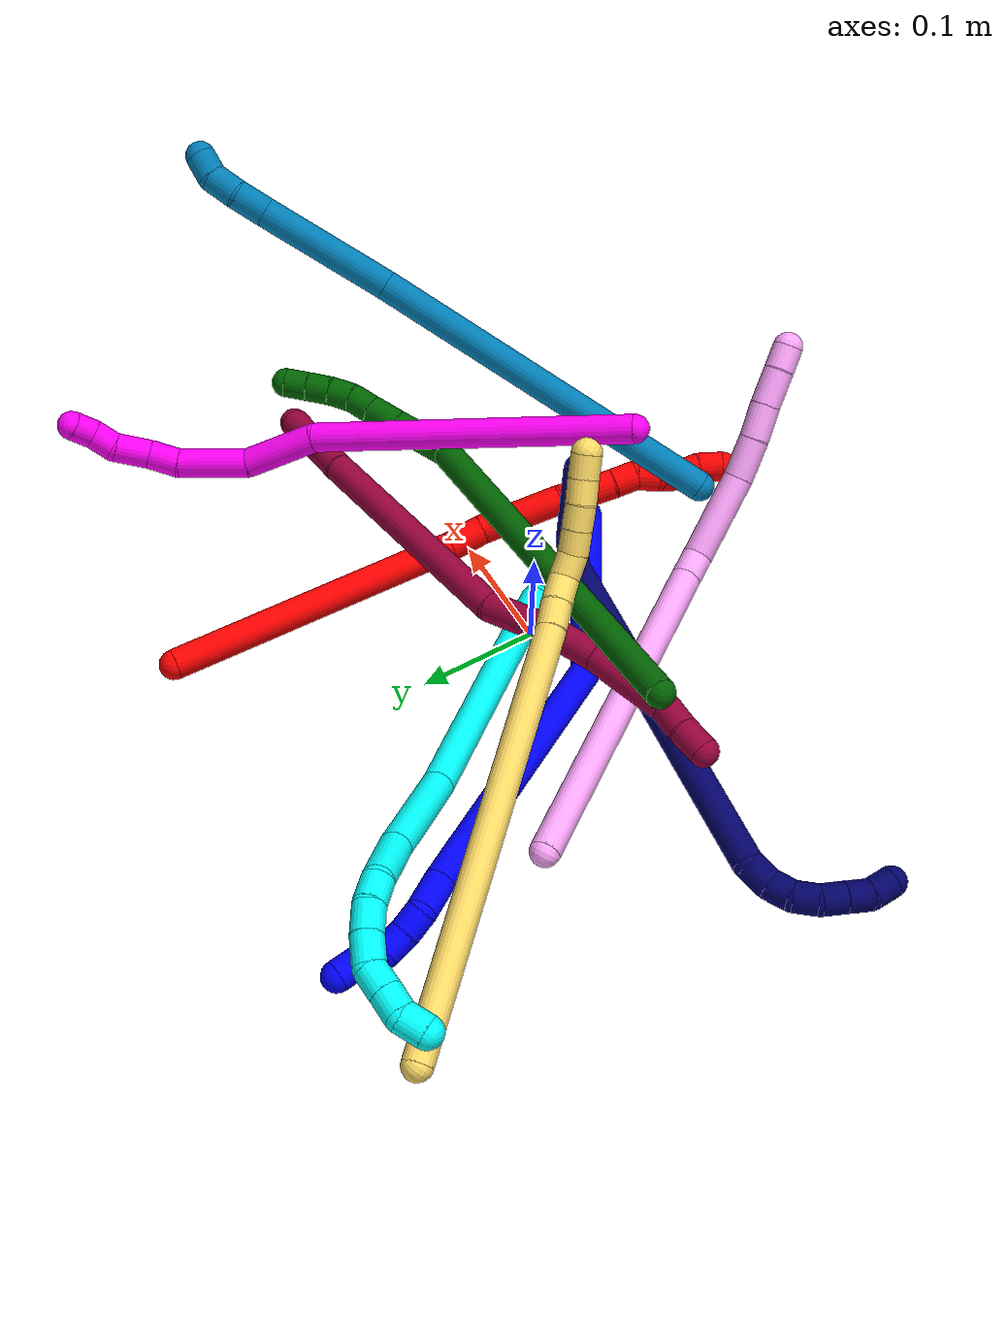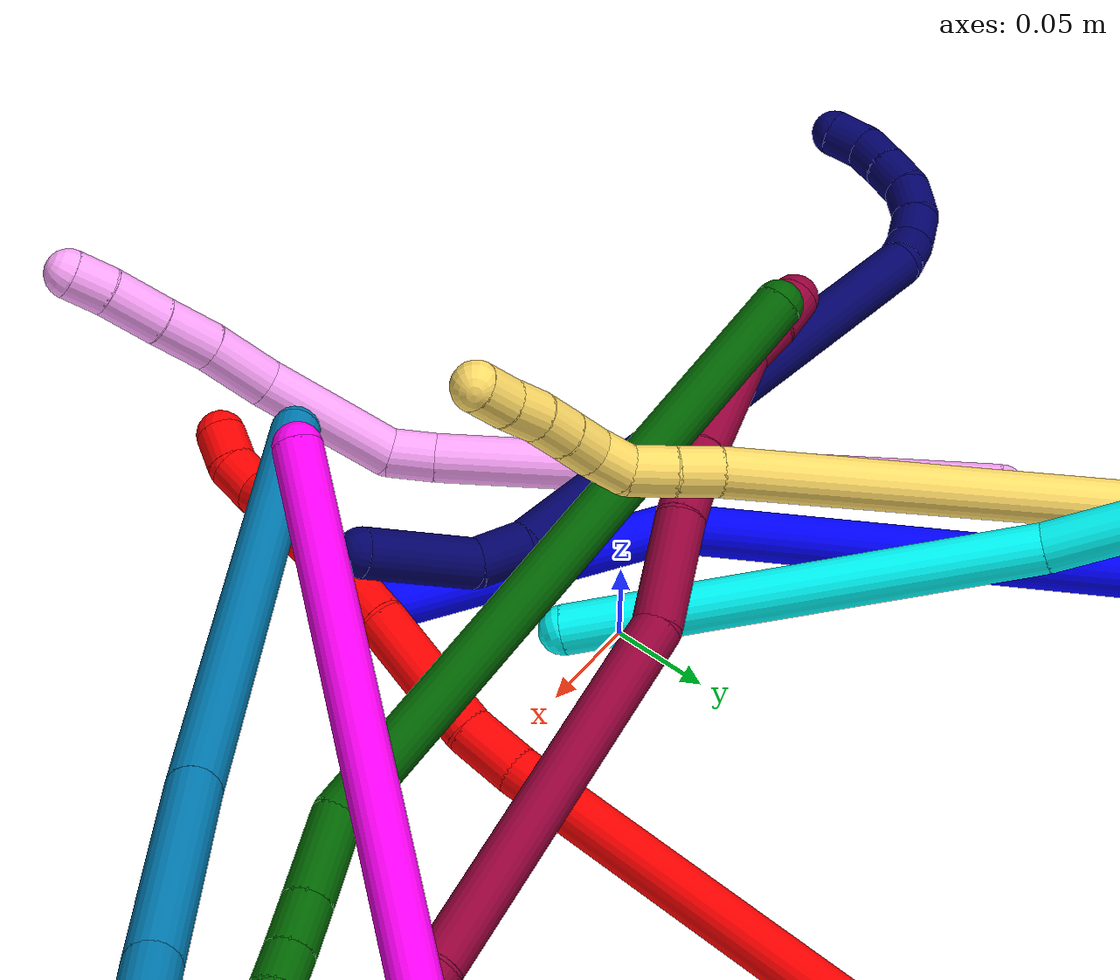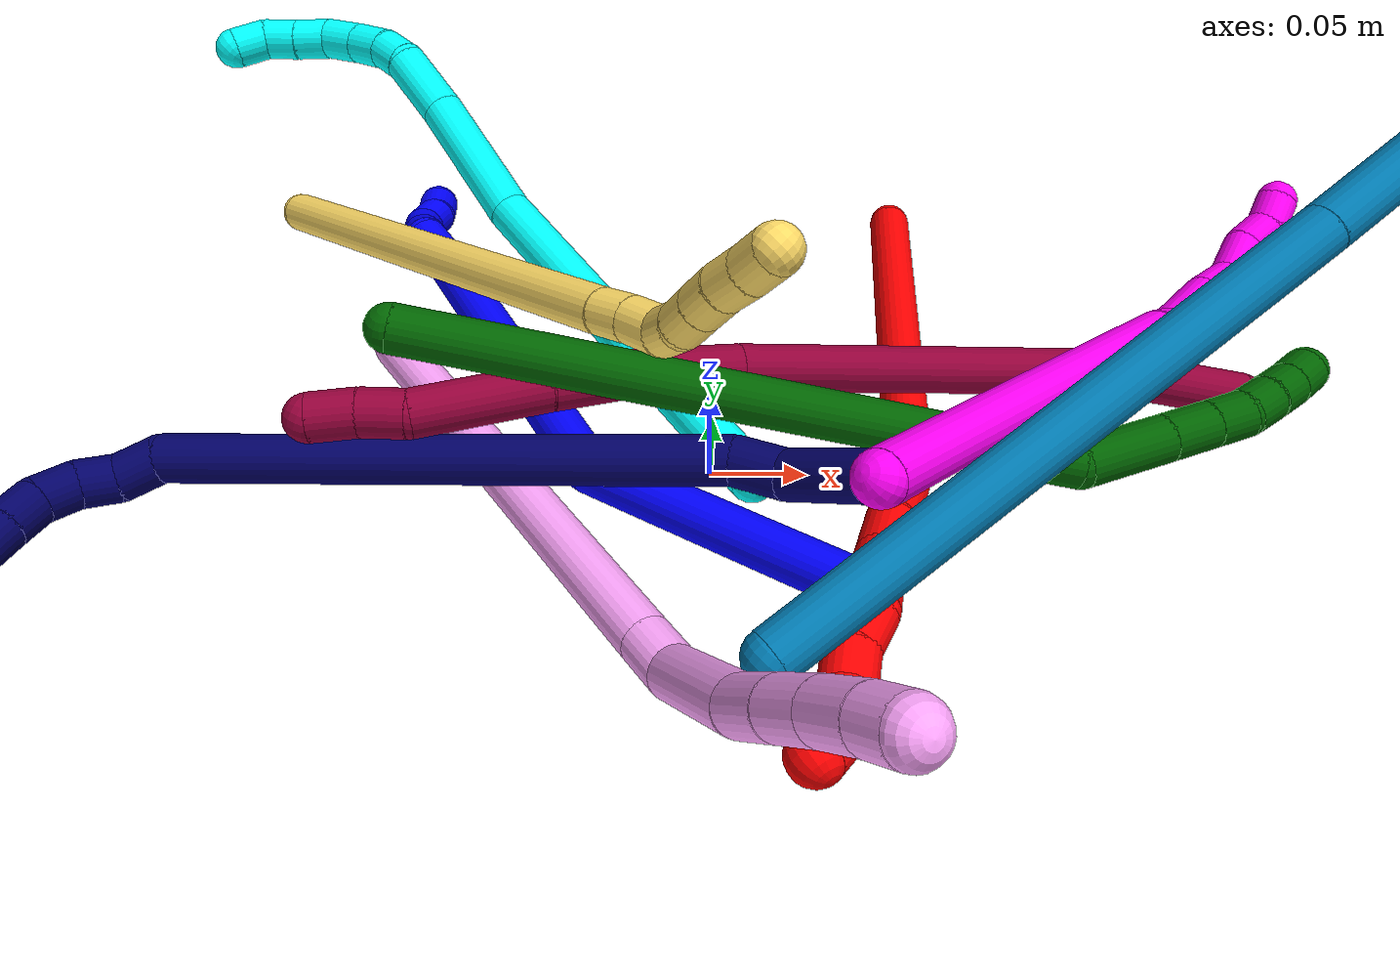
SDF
<sdf version="1.7">
 <world name="default">
  <plugin name="TubeGeneratorPlugin" filename="libtube_generator_plugin.so"/>
  <model name="photoneo_s_sensor">
   <static>1</static>
   <pose>0 0 2 1.57079 1.57079 3.14159</pose>
   <link name="link">
    <inertial><mass>0.1</mass></inertial>
    <sensor name="sensor" type="depth">
     <update_rate>30</update_rate>
     <camera>
      <horizontal_fov>1.22</horizontal_fov>
      <image><width>1920</width><height>1200</height><format>B8G8R8</format></image>
      <clip><near>0.1</near><far>2</far></clip>
      <depth_camera><output>points</output></depth_camera>
     </camera>
     <plugin name="camera_plugin" filename="libgazebo_ros_depth_camera.so">
      <baseline>0.2</baseline>
      <alwaysOn>1</alwaysOn>
      <updateRate>0.0</updateRate>
      <cameraName>camera_ir</cameraName>
      <imageTopicName>/camera/color/image_raw</imageTopicName>
      <cameraInfoTopicName>/camera/color/camera_info</cameraInfoTopicName>
      <depthImageTopicName>/camera/depth/image_raw</depthImageTopicName>
      <depthImageCameraInfoTopicName>/camera/depth/camera_info</depthImageCameraInfoTopicName>
      <pointCloudTopicName>/camera/depth/points</pointCloudTopicName>
      <frameName>fr_optical</frameName>
      <pointCloudCutoff>0.1</pointCloudCutoff>
      <pointCloudCutoffMax>2.0</pointCloudCutoffMax>
      <distortionK1>0</distortionK1>
      <distortionK2>0</distortionK2>
      <distortionK3>0</distortionK3>
      <distortionT1>0</distortionT1>
      <distortionT2>0</distortionT2>
      <CxPrime>0</CxPrime>
      <Cx>0</Cx>
      <Cy>0</Cy>
      <focalLength>0</focalLength>
      <hackBaseline>0</hackBaseline>
     </plugin>
    </sensor>
   </link>
  </model>
  <gravity>0 0 -9.8</gravity>
  <magnetic_field>6e-06 2.3e-05 -4.2e-05</magnetic_field>
  <atmosphere type="adiabatic"/>
  <physics name="default_physics" default="0" type="ode">
   <max_step_size>0.003</max_step_size>
   <real_time_factor>1</real_time_factor>
   <real_time_update_rate>1000</real_time_update_rate>
   <max_contacts>10000</max_contacts>
   <ode>
    <solver>
     <type>quick</type>
     <iters>100</iters>
     <sor>1.3</sor>
     <use_dynamic_moi_rescaling>0</use_dynamic_moi_rescaling>
    </solver>
    <constraints>
     <contact_max_correcting_vel>0</contact_max_correcting_vel>
     <contact_surface_layer>0.001</contact_surface_layer>
     <cfm>0</cfm>
     <erp>0.2</erp>
    </constraints>
   </ode>
  </physics>
  <scene><ambient>0.4 0.4 0.4 1</ambient><background>0.7 0.7 0.7 1</background><shadows>0</shadows></scene>
  <audio><device>default</device></audio>
  <spherical_coordinates>
   <surface_model>EARTH_WGS84</surface_model>
   <latitude_deg>0</latitude_deg>
   <longitude_deg>0</longitude_deg>
   <elevation>0</elevation>
   <heading_deg>0</heading_deg>
  </spherical_coordinates>
  <model name="bin">
   <static>1</static>
   <link name="bottom">
    <collision name="collision-bottom">
     <pose>0 0 -0.01 0 -0 0</pose>
     <geometry><box><size>0.8 0.6 0.02</size></box></geometry>
     <surface>
      <friction><ode><mu>100</mu><mu2>100</mu2></ode></friction>
      <contact><collide_bitmask>65535</collide_bitmask></contact>
     </surface>
    </collision>
   </link>
   <link name="west_wall">
    <collision name="collision-west_wall">
     <pose>-0.41 0 0.1 0 -0 0</pose>
     <geometry><box><size>0.02 0.6 0.2</size></box></geometry>
     <surface>
      <friction><ode><mu>100</mu><mu2>100</mu2></ode></friction>
      <contact><collide_bitmask>65535</collide_bitmask></contact>
     </surface>
    </collision>
   </link>
   <link name="east_wall">
    <collision name="collision-east_wall">
     <pose>0.41 0 0.1 0 -0 0</pose>
     <geometry><box><size>0.02 0.6 0.2</size></box></geometry>
     <surface>
      <friction><ode><mu>100</mu><mu2>100</mu2></ode></friction>
      <contact><collide_bitmask>65535</collide_bitmask></contact>
     </surface>
    </collision>
   </link>
   <link name="south_wall">
    <collision name="collision-south_wall">
     <pose>0 -0.31 0.1 0 -0 0</pose>
     <geometry><box><size>0.8 0.02 0.2</size></box></geometry>
     <surface>
      <friction><ode><mu>100</mu><mu2>100</mu2></ode></friction>
      <contact><collide_bitmask>65535</collide_bitmask></contact>
     </surface>
    </collision>
   </link>
   <link name="north_wall">
    <collision name="collision-north_wall">
     <pose>0 0.31 0.1 0 -0 0</pose>
     <geometry><box><size>0.8 0.02 0.2</size></box></geometry>
     <surface>
      <friction><ode><mu>100</mu><mu2>100</mu2></ode></friction>
      <contact><collide_bitmask>65535</collide_bitmask></contact>
     </surface>
    </collision>
   </link>
  </model>
  <model name="1">
   <static>0</static>
   <link name="1">
    <collision name="collision-cylinder-e_1_1_4">
     <pose>-0.035185 0.035202 0.062332 -0.514101 -0.456832 0.122067</pose>
     <geometry><cylinder><radius>0.0125</radius><length>0.15953</length></cylinder></geometry>
     <surface>
      <friction><ode><mu>1.16</mu><mu2>1.16</mu2><slip1>0</slip1><slip2>0</slip2></ode></friction>
      <contact><ode><kp>1e+06</kp><kd>1</kd><max_vel>0</max_vel><min_depth>0.001</min_depth></ode></contact>
     </surface>
    </collision>
    <visual name="visual-cylinder-e_1_1_4">
     <pose>-0.035185 0.035202 0.062332 -0.514101 -0.456832 0.122067</pose>
     <geometry><cylinder><radius>0.0125</radius><length>0.15953</length></cylinder></geometry>
     <material><ambient>0 0 1 1</ambient></material>
    </visual>
    <collision name="collision-cylinder-e_2_4_5">
     <pose>-0.081371 0.157982 0.197518 -0.876915 -0.096266 0.045166</pose>
     <geometry><cylinder><radius>0.0125</radius><length>0.228896</length></cylinder></geometry>
     <surface>
      <friction><ode><mu>1.16</mu><mu2>1.16</mu2><slip1>0</slip1><slip2>0</slip2></ode></friction>
      <contact><ode><kp>1e+06</kp><kd>1</kd><max_vel>0</max_vel><min_depth>0.001</min_depth></ode></contact>
     </surface>
    </collision>
    <visual name="visual-cylinder-e_2_4_5">
     <pose>-0.081371 0.157982 0.197518 -0.876915 -0.096266 0.045166</pose>
     <geometry><cylinder><radius>0.0125</radius><length>0.228896</length></cylinder></geometry>
     <material><ambient>0 0 1 1</ambient></material>
    </visual>
    <collision name="collision-cylinder-e_3_5_6">
     <pose>-0.094119 0.256439 0.280994 -0.797368 -0.114472 0.048264</pose>
     <geometry><cylinder><radius>0.0125</radius><length>0.030611</length></cylinder></geometry>
     <surface>
      <friction><ode><mu>1.16</mu><mu2>1.16</mu2><slip1>0</slip1><slip2>0</slip2></ode></friction>
      <contact><ode><kp>1e+06</kp><kd>1</kd><max_vel>0</max_vel><min_depth>0.001</min_depth></ode></contact>
     </surface>
    </collision>
    <visual name="visual-cylinder-e_3_5_6">
     <pose>-0.094119 0.256439 0.280994 -0.797368 -0.114472 0.048264</pose>
     <geometry><cylinder><radius>0.0125</radius><length>0.030611</length></cylinder></geometry>
     <material><ambient>0 0 1 1</ambient></material>
    </visual>
    <collision name="collision-cylinder-e_4_6_7">
     <pose>-0.098407 0.276807 0.294485 -1.27721 -0.250798 0.186626</pose>
     <geometry><cylinder><radius>0.0125</radius><length>0.020465</length></cylinder></geometry>
     <surface>
      <friction><ode><mu>1.16</mu><mu2>1.16</mu2><slip1>0</slip1><slip2>0</slip2></ode></friction>
      <contact><ode><kp>1e+06</kp><kd>1</kd><max_vel>0</max_vel><min_depth>0.001</min_depth></ode></contact>
     </surface>
    </collision>
    <visual name="visual-cylinder-e_4_6_7">
     <pose>-0.098407 0.276807 0.294485 -1.27721 -0.250798 0.186626</pose>
     <geometry><cylinder><radius>0.0125</radius><length>0.020465</length></cylinder></geometry>
     <material><ambient>0 0 1 1</ambient></material>
    </visual>
    <collision name="collision-cylinder-e_5_7_8">
     <pose>-0.102002 0.296021 0.300208 -1.28537 -0.103709 0.07768</pose>
     <geometry><cylinder><radius>0.0125</radius><length>0.020382</length></cylinder></geometry>
     <surface>
      <friction><ode><mu>1.16</mu><mu2>1.16</mu2><slip1>0</slip1><slip2>0</slip2></ode></friction>
      <contact><ode><kp>1e+06</kp><kd>1</kd><max_vel>0</max_vel><min_depth>0.001</min_depth></ode></contact>
     </surface>
    </collision>
    <visual name="visual-cylinder-e_5_7_8">
     <pose>-0.102002 0.296021 0.300208 -1.28537 -0.103709 0.07768</pose>
     <geometry><cylinder><radius>0.0125</radius><length>0.020382</length></cylinder></geometry>
     <material><ambient>0 0 1 1</ambient></material>
    </visual>
    <collision name="collision-cylinder-e_6_8_9">
     <pose>-0.100186 0.315313 0.303796 -1.49415 0.290772 -0.269566</pose>
     <geometry><cylinder><radius>0.0125</radius><length>0.020027</length></cylinder></geometry>
     <surface>
      <friction><ode><mu>1.16</mu><mu2>1.16</mu2><slip1>0</slip1><slip2>0</slip2></ode></friction>
      <contact><ode><kp>1e+06</kp><kd>1</kd><max_vel>0</max_vel><min_depth>0.001</min_depth></ode></contact>
     </surface>
    </collision>
    <visual name="visual-cylinder-e_6_8_9">
     <pose>-0.100186 0.315313 0.303796 -1.49415 0.290772 -0.269566</pose>
     <geometry><cylinder><radius>0.0125</radius><length>0.020027</length></cylinder></geometry>
     <material><ambient>0 0 1 1</ambient></material>
    </visual>
    <collision name="collision-cylinder-e_7_9_2">
     <pose>-0.096123 0.334279 0.307857 -1.23075 0.118917 -0.084118</pose>
     <geometry><cylinder><radius>0.0125</radius><length>0.020087</length></cylinder></geometry>
     <surface>
      <friction><ode><mu>1.16</mu><mu2>1.16</mu2><slip1>0</slip1><slip2>0</slip2></ode></friction>
      <contact><ode><kp>1e+06</kp><kd>1</kd><max_vel>0</max_vel><min_depth>0.001</min_depth></ode></contact>
     </surface>
    </collision>
    <visual name="visual-cylinder-e_7_9_2">
     <pose>-0.096123 0.334279 0.307857 -1.23075 0.118917 -0.084118</pose>
     <geometry><cylinder><radius>0.0125</radius><length>0.020087</length></cylinder></geometry>
     <material><ambient>0 0 1 1</ambient></material>
    </visual>
    <collision name="collision-sphere-2">
     <pose>-0.094932 0.343681 0.311183 0 -0 0</pose>
     <geometry><sphere><radius>0.0125</radius></sphere></geometry>
     <surface>
      <friction><ode><mu>1.16</mu><mu2>1.16</mu2><slip1>0</slip1><slip2>0</slip2></ode></friction>
      <contact><ode><kp>1e+06</kp><kd>1</kd><max_vel>0</max_vel><min_depth>0.001</min_depth></ode></contact>
     </surface>
    </collision>
    <visual name="visual-sphere-2">
     <pose>-0.094932 0.343681 0.311183 0 -0 0</pose>
     <geometry><sphere><radius>0.0125</radius></sphere></geometry>
     <material><ambient>0 0 1 1</ambient></material>
    </visual>
    <collision name="collision-sphere-9">
     <pose>-0.097315 0.324878 0.304531 0 -0 0</pose>
     <geometry><sphere><radius>0.0125</radius></sphere></geometry>
     <surface>
      <friction><ode><mu>1.16</mu><mu2>1.16</mu2><slip1>0</slip1><slip2>0</slip2></ode></friction>
      <contact><ode><kp>1e+06</kp><kd>1</kd><max_vel>0</max_vel><min_depth>0.001</min_depth></ode></contact>
     </surface>
    </collision>
    <visual name="visual-sphere-9">
     <pose>-0.097315 0.324878 0.304531 0 -0 0</pose>
     <geometry><sphere><radius>0.0125</radius></sphere></geometry>
     <material><ambient>0 0 1 1</ambient></material>
    </visual>
    <collision name="collision-sphere-4">
     <pose>-0.07037 0.070405 0.124664 0 -0 0</pose>
     <geometry><sphere><radius>0.0125</radius></sphere></geometry>
     <surface>
      <friction><ode><mu>1.16</mu><mu2>1.16</mu2><slip1>0</slip1><slip2>0</slip2></ode></friction>
      <contact><ode><kp>1e+06</kp><kd>1</kd><max_vel>0</max_vel><min_depth>0.001</min_depth></ode></contact>
     </surface>
    </collision>
    <visual name="visual-sphere-4">
     <pose>-0.07037 0.070405 0.124664 0 -0 0</pose>
     <geometry><sphere><radius>0.0125</radius></sphere></geometry>
     <material><ambient>0 0 1 1</ambient></material>
    </visual>
    <collision name="collision-sphere-1">
     <geometry><sphere><radius>0.0125</radius></sphere></geometry>
     <surface>
      <friction><ode><mu>1.16</mu><mu2>1.16</mu2><slip1>0</slip1><slip2>0</slip2></ode></friction>
      <contact><ode><kp>1e+06</kp><kd>1</kd><max_vel>0</max_vel><min_depth>0.001</min_depth></ode></contact>
     </surface>
    </collision>
    <visual name="visual-sphere-1">
     <geometry><sphere><radius>0.0125</radius></sphere></geometry>
     <material><ambient>0 0 1 1</ambient></material>
    </visual>
    <collision name="collision-sphere-8">
     <pose>-0.103057 0.305748 0.303062 0 -0 0</pose>
     <geometry><sphere><radius>0.0125</radius></sphere></geometry>
     <surface>
      <friction><ode><mu>1.16</mu><mu2>1.16</mu2><slip1>0</slip1><slip2>0</slip2></ode></friction>
      <contact><ode><kp>1e+06</kp><kd>1</kd><max_vel>0</max_vel><min_depth>0.001</min_depth></ode></contact>
     </surface>
    </collision>
    <visual name="visual-sphere-8">
     <pose>-0.103057 0.305748 0.303062 0 -0 0</pose>
     <geometry><sphere><radius>0.0125</radius></sphere></geometry>
     <material><ambient>0 0 1 1</ambient></material>
    </visual>
    <collision name="collision-sphere-5">
     <pose>-0.092371 0.245559 0.270372 0 -0 0</pose>
     <geometry><sphere><radius>0.0125</radius></sphere></geometry>
     <surface>
      <friction><ode><mu>1.16</mu><mu2>1.16</mu2><slip1>0</slip1><slip2>0</slip2></ode></friction>
      <contact><ode><kp>1e+06</kp><kd>1</kd><max_vel>0</max_vel><min_depth>0.001</min_depth></ode></contact>
     </surface>
    </collision>
    <visual name="visual-sphere-5">
     <pose>-0.092371 0.245559 0.270372 0 -0 0</pose>
     <geometry><sphere><radius>0.0125</radius></sphere></geometry>
     <material><ambient>0 0 1 1</ambient></material>
    </visual>
    <collision name="collision-sphere-6">
     <pose>-0.095868 0.267318 0.291617 0 -0 0</pose>
     <geometry><sphere><radius>0.0125</radius></sphere></geometry>
     <surface>
      <friction><ode><mu>1.16</mu><mu2>1.16</mu2><slip1>0</slip1><slip2>0</slip2></ode></friction>
      <contact><ode><kp>1e+06</kp><kd>1</kd><max_vel>0</max_vel><min_depth>0.001</min_depth></ode></contact>
     </surface>
    </collision>
    <visual name="visual-sphere-6">
     <pose>-0.095868 0.267318 0.291617 0 -0 0</pose>
     <geometry><sphere><radius>0.0125</radius></sphere></geometry>
     <material><ambient>0 0 1 1</ambient></material>
    </visual>
    <collision name="collision-sphere-7">
     <pose>-0.100947 0.286295 0.297354 0 -0 0</pose>
     <geometry><sphere><radius>0.0125</radius></sphere></geometry>
     <surface>
      <friction><ode><mu>1.16</mu><mu2>1.16</mu2><slip1>0</slip1><slip2>0</slip2></ode></friction>
      <contact><ode><kp>1e+06</kp><kd>1</kd><max_vel>0</max_vel><min_depth>0.001</min_depth></ode></contact>
     </surface>
    </collision>
    <visual name="visual-sphere-7">
     <pose>-0.100947 0.286295 0.297354 0 -0 0</pose>
     <geometry><sphere><radius>0.0125</radius></sphere></geometry>
     <material><ambient>0 0 1 1</ambient></material>
    </visual>
    <inertial>
     <pose>-0.0703 0.148711 0.176341 0 -0 0</pose>
     <mass>0.5</mass>
     <inertia>
      <ixx>0.001394</ixx>
      <ixy>0</ixy>
      <ixz>0</ixz>
      <iyy>0.001069</iyy>
      <iyz>0</iyz>
      <izz>-0.000658</izz>
     </inertia>
    </inertial>
   </link>
   <pose>0.074325 -0.100117 0.011489 -0.525991 -0.793883 0.322089</pose>
  </model>
  <model name="2">
   <static>0</static>
   <link name="2">
    <collision name="collision-cylinder-e_1_1_4">
     <pose>-0.024738 -0.073642 -0.098688 2.50052 -0.198258 -0.58214</pose>
     <geometry><cylinder><radius>0.0125</radius><length>0.251193</length></cylinder></geometry>
     <surface>
      <friction><ode><mu>1.16</mu><mu2>1.16</mu2><slip1>0</slip1><slip2>0</slip2></ode></friction>
      <contact><ode><kp>1e+06</kp><kd>1</kd><max_vel>0</max_vel><min_depth>0.001</min_depth></ode></contact>
     </surface>
    </collision>
    <visual name="visual-cylinder-e_1_1_4">
     <pose>-0.024738 -0.073642 -0.098688 2.50052 -0.198258 -0.58214</pose>
     <geometry><cylinder><radius>0.0125</radius><length>0.251193</length></cylinder></geometry>
     <material><ambient>1 0 0 1</ambient></material>
    </visual>
    <collision name="collision-cylinder-e_2_4_5">
     <pose>-0.050624 -0.157809 -0.208819 2.39795 -0.073718 -0.188564</pose>
     <geometry><cylinder><radius>0.0125</radius><length>0.031178</length></cylinder></geometry>
     <surface>
      <friction><ode><mu>1.16</mu><mu2>1.16</mu2><slip1>0</slip1><slip2>0</slip2></ode></friction>
      <contact><ode><kp>1e+06</kp><kd>1</kd><max_vel>0</max_vel><min_depth>0.001</min_depth></ode></contact>
     </surface>
    </collision>
    <visual name="visual-cylinder-e_2_4_5">
     <pose>-0.050624 -0.157809 -0.208819 2.39795 -0.073718 -0.188564</pose>
     <geometry><cylinder><radius>0.0125</radius><length>0.031178</length></cylinder></geometry>
     <material><ambient>1 0 0 1</ambient></material>
    </visual>
    <collision name="collision-cylinder-e_3_5_6">
     <pose>-0.056963 -0.19606 -0.241227 2.21824 -0.148247 -0.29632</pose>
     <geometry><cylinder><radius>0.0125</radius><length>0.070293</length></cylinder></geometry>
     <surface>
      <friction><ode><mu>1.16</mu><mu2>1.16</mu2><slip1>0</slip1><slip2>0</slip2></ode></friction>
      <contact><ode><kp>1e+06</kp><kd>1</kd><max_vel>0</max_vel><min_depth>0.001</min_depth></ode></contact>
     </surface>
    </collision>
    <visual name="visual-cylinder-e_3_5_6">
     <pose>-0.056963 -0.19606 -0.241227 2.21824 -0.148247 -0.29632</pose>
     <geometry><cylinder><radius>0.0125</radius><length>0.070293</length></cylinder></geometry>
     <material><ambient>1 0 0 1</ambient></material>
    </visual>
    <collision name="collision-cylinder-e_4_6_7">
     <pose>-0.066007 -0.233097 -0.270726 2.31264 -0.296072 -0.653595</pose>
     <geometry><cylinder><radius>0.0125</radius><length>0.026408</length></cylinder></geometry>
     <surface>
      <friction><ode><mu>1.16</mu><mu2>1.16</mu2><slip1>0</slip1><slip2>0</slip2></ode></friction>
      <contact><ode><kp>1e+06</kp><kd>1</kd><max_vel>0</max_vel><min_depth>0.001</min_depth></ode></contact>
     </surface>
    </collision>
    <visual name="visual-cylinder-e_4_6_7">
     <pose>-0.066007 -0.233097 -0.270726 2.31264 -0.296072 -0.653595</pose>
     <geometry><cylinder><radius>0.0125</radius><length>0.026408</length></cylinder></geometry>
     <material><ambient>1 0 0 1</ambient></material>
    </visual>
    <collision name="collision-cylinder-e_5_7_8">
     <pose>-0.072007 -0.250317 -0.285723 2.25597 -0.207259 -0.43179</pose>
     <geometry><cylinder><radius>0.0125</radius><length>0.020876</length></cylinder></geometry>
     <surface>
      <friction><ode><mu>1.16</mu><mu2>1.16</mu2><slip1>0</slip1><slip2>0</slip2></ode></friction>
      <contact><ode><kp>1e+06</kp><kd>1</kd><max_vel>0</max_vel><min_depth>0.001</min_depth></ode></contact>
     </surface>
    </collision>
    <visual name="visual-cylinder-e_5_7_8">
     <pose>-0.072007 -0.250317 -0.285723 2.25597 -0.207259 -0.43179</pose>
     <geometry><cylinder><radius>0.0125</radius><length>0.020876</length></cylinder></geometry>
     <material><ambient>1 0 0 1</ambient></material>
    </visual>
    <collision name="collision-cylinder-e_6_8_9">
     <pose>-0.076047 -0.265207 -0.299129 2.3534 -0.189829 -0.450102</pose>
     <geometry><cylinder><radius>0.0125</radius><length>0.02005</length></cylinder></geometry>
     <surface>
      <friction><ode><mu>1.16</mu><mu2>1.16</mu2><slip1>0</slip1><slip2>0</slip2></ode></friction>
      <contact><ode><kp>1e+06</kp><kd>1</kd><max_vel>0</max_vel><min_depth>0.001</min_depth></ode></contact>
     </surface>
    </collision>
    <visual name="visual-cylinder-e_6_8_9">
     <pose>-0.076047 -0.265207 -0.299129 2.3534 -0.189829 -0.450102</pose>
     <geometry><cylinder><radius>0.0125</radius><length>0.02005</length></cylinder></geometry>
     <material><ambient>1 0 0 1</ambient></material>
    </visual>
    <collision name="collision-cylinder-e_7_9_10">
     <pose>-0.083623 -0.278379 -0.31149 2.28982 -0.604622 -1.20452</pose>
     <geometry><cylinder><radius>0.0125</radius><length>0.02</length></cylinder></geometry>
     <surface>
      <friction><ode><mu>1.16</mu><mu2>1.16</mu2><slip1>0</slip1><slip2>0</slip2></ode></friction>
      <contact><ode><kp>1e+06</kp><kd>1</kd><max_vel>0</max_vel><min_depth>0.001</min_depth></ode></contact>
     </surface>
    </collision>
    <visual name="visual-cylinder-e_7_9_10">
     <pose>-0.083623 -0.278379 -0.31149 2.28982 -0.604622 -1.20452</pose>
     <geometry><cylinder><radius>0.0125</radius><length>0.02</length></cylinder></geometry>
     <material><ambient>1 0 0 1</ambient></material>
    </visual>
    <collision name="collision-cylinder-e_8_10_11">
     <pose>-0.094587 -0.288203 -0.324585 2.69953 -0.556147 -1.8079</pose>
     <geometry><cylinder><radius>0.0125</radius><length>0.02</length></cylinder></geometry>
     <surface>
      <friction><ode><mu>1.16</mu><mu2>1.16</mu2><slip1>0</slip1><slip2>0</slip2></ode></friction>
      <contact><ode><kp>1e+06</kp><kd>1</kd><max_vel>0</max_vel><min_depth>0.001</min_depth></ode></contact>
     </surface>
    </collision>
    <visual name="visual-cylinder-e_8_10_11">
     <pose>-0.094587 -0.288203 -0.324585 2.69953 -0.556147 -1.8079</pose>
     <geometry><cylinder><radius>0.0125</radius><length>0.02</length></cylinder></geometry>
     <material><ambient>1 0 0 1</ambient></material>
    </visual>
    <collision name="collision-cylinder-e_9_11_12">
     <pose>-0.101597 -0.299079 -0.338936 2.31534 -0.173984 -0.392779</pose>
     <geometry><cylinder><radius>0.0125</radius><length>0.020001</length></cylinder></geometry>
     <surface>
      <friction><ode><mu>1.16</mu><mu2>1.16</mu2><slip1>0</slip1><slip2>0</slip2></ode></friction>
      <contact><ode><kp>1e+06</kp><kd>1</kd><max_vel>0</max_vel><min_depth>0.001</min_depth></ode></contact>
     </surface>
    </collision>
    <visual name="visual-cylinder-e_9_11_12">
     <pose>-0.101597 -0.299079 -0.338936 2.31534 -0.173984 -0.392779</pose>
     <geometry><cylinder><radius>0.0125</radius><length>0.020001</length></cylinder></geometry>
     <material><ambient>1 0 0 1</ambient></material>
    </visual>
    <collision name="collision-cylinder-e_10_12_2">
     <pose>-0.107525 -0.314514 -0.349521 2.01616 -0.433088 -0.67119</pose>
     <geometry><cylinder><radius>0.0125</radius><length>0.02</length></cylinder></geometry>
     <surface>
      <friction><ode><mu>1.16</mu><mu2>1.16</mu2><slip1>0</slip1><slip2>0</slip2></ode></friction>
      <contact><ode><kp>1e+06</kp><kd>1</kd><max_vel>0</max_vel><min_depth>0.001</min_depth></ode></contact>
     </surface>
    </collision>
    <visual name="visual-cylinder-e_10_12_2">
     <pose>-0.107525 -0.314514 -0.349521 2.01616 -0.433088 -0.67119</pose>
     <geometry><cylinder><radius>0.0125</radius><length>0.02</length></cylinder></geometry>
     <material><ambient>1 0 0 1</ambient></material>
    </visual>
    <collision name="collision-sphere-2">
     <pose>-0.111722 -0.322706 -0.353431 0 -0 0</pose>
     <geometry><sphere><radius>0.0125</radius></sphere></geometry>
     <surface>
      <friction><ode><mu>1.16</mu><mu2>1.16</mu2><slip1>0</slip1><slip2>0</slip2></ode></friction>
      <contact><ode><kp>1e+06</kp><kd>1</kd><max_vel>0</max_vel><min_depth>0.001</min_depth></ode></contact>
     </surface>
    </collision>
    <visual name="visual-sphere-2">
     <pose>-0.111722 -0.322706 -0.353431 0 -0 0</pose>
     <geometry><sphere><radius>0.0125</radius></sphere></geometry>
     <material><ambient>1 0 0 1</ambient></material>
    </visual>
    <collision name="collision-sphere-12">
     <pose>-0.103328 -0.306323 -0.345611 0 -0 0</pose>
     <geometry><sphere><radius>0.0125</radius></sphere></geometry>
     <surface>
      <friction><ode><mu>1.16</mu><mu2>1.16</mu2><slip1>0</slip1><slip2>0</slip2></ode></friction>
      <contact><ode><kp>1e+06</kp><kd>1</kd><max_vel>0</max_vel><min_depth>0.001</min_depth></ode></contact>
     </surface>
    </collision>
    <visual name="visual-sphere-12">
     <pose>-0.103328 -0.306323 -0.345611 0 -0 0</pose>
     <geometry><sphere><radius>0.0125</radius></sphere></geometry>
     <material><ambient>1 0 0 1</ambient></material>
    </visual>
    <collision name="collision-sphere-11">
     <pose>-0.099866 -0.291836 -0.332262 0 -0 0</pose>
     <geometry><sphere><radius>0.0125</radius></sphere></geometry>
     <surface>
      <friction><ode><mu>1.16</mu><mu2>1.16</mu2><slip1>0</slip1><slip2>0</slip2></ode></friction>
      <contact><ode><kp>1e+06</kp><kd>1</kd><max_vel>0</max_vel><min_depth>0.001</min_depth></ode></contact>
     </surface>
    </collision>
    <visual name="visual-sphere-11">
     <pose>-0.099866 -0.291836 -0.332262 0 -0 0</pose>
     <geometry><sphere><radius>0.0125</radius></sphere></geometry>
     <material><ambient>1 0 0 1</ambient></material>
    </visual>
    <collision name="collision-sphere-10">
     <pose>-0.089308 -0.284569 -0.316909 0 -0 0</pose>
     <geometry><sphere><radius>0.0125</radius></sphere></geometry>
     <surface>
      <friction><ode><mu>1.16</mu><mu2>1.16</mu2><slip1>0</slip1><slip2>0</slip2></ode></friction>
      <contact><ode><kp>1e+06</kp><kd>1</kd><max_vel>0</max_vel><min_depth>0.001</min_depth></ode></contact>
     </surface>
    </collision>
    <visual name="visual-sphere-10">
     <pose>-0.089308 -0.284569 -0.316909 0 -0 0</pose>
     <geometry><sphere><radius>0.0125</radius></sphere></geometry>
     <material><ambient>1 0 0 1</ambient></material>
    </visual>
    <collision name="collision-sphere-9">
     <pose>-0.077938 -0.272188 -0.306071 0 -0 0</pose>
     <geometry><sphere><radius>0.0125</radius></sphere></geometry>
     <surface>
      <friction><ode><mu>1.16</mu><mu2>1.16</mu2><slip1>0</slip1><slip2>0</slip2></ode></friction>
      <contact><ode><kp>1e+06</kp><kd>1</kd><max_vel>0</max_vel><min_depth>0.001</min_depth></ode></contact>
     </surface>
    </collision>
    <visual name="visual-sphere-9">
     <pose>-0.077938 -0.272188 -0.306071 0 -0 0</pose>
     <geometry><sphere><radius>0.0125</radius></sphere></geometry>
     <material><ambient>1 0 0 1</ambient></material>
    </visual>
    <collision name="collision-sphere-4">
     <pose>-0.049475 -0.147284 -0.197376 0 -0 0</pose>
     <geometry><sphere><radius>0.0125</radius></sphere></geometry>
     <surface>
      <friction><ode><mu>1.16</mu><mu2>1.16</mu2><slip1>0</slip1><slip2>0</slip2></ode></friction>
      <contact><ode><kp>1e+06</kp><kd>1</kd><max_vel>0</max_vel><min_depth>0.001</min_depth></ode></contact>
     </surface>
    </collision>
    <visual name="visual-sphere-4">
     <pose>-0.049475 -0.147284 -0.197376 0 -0 0</pose>
     <geometry><sphere><radius>0.0125</radius></sphere></geometry>
     <material><ambient>1 0 0 1</ambient></material>
    </visual>
    <collision name="collision-sphere-1">
     <geometry><sphere><radius>0.0125</radius></sphere></geometry>
     <surface>
      <friction><ode><mu>1.16</mu><mu2>1.16</mu2><slip1>0</slip1><slip2>0</slip2></ode></friction>
      <contact><ode><kp>1e+06</kp><kd>1</kd><max_vel>0</max_vel><min_depth>0.001</min_depth></ode></contact>
     </surface>
    </collision>
    <visual name="visual-sphere-1">
     <geometry><sphere><radius>0.0125</radius></sphere></geometry>
     <material><ambient>1 0 0 1</ambient></material>
    </visual>
    <collision name="collision-sphere-8">
     <pose>-0.074155 -0.258226 -0.292187 0 -0 0</pose>
     <geometry><sphere><radius>0.0125</radius></sphere></geometry>
     <surface>
      <friction><ode><mu>1.16</mu><mu2>1.16</mu2><slip1>0</slip1><slip2>0</slip2></ode></friction>
      <contact><ode><kp>1e+06</kp><kd>1</kd><max_vel>0</max_vel><min_depth>0.001</min_depth></ode></contact>
     </surface>
    </collision>
    <visual name="visual-sphere-8">
     <pose>-0.074155 -0.258226 -0.292187 0 -0 0</pose>
     <geometry><sphere><radius>0.0125</radius></sphere></geometry>
     <material><ambient>1 0 0 1</ambient></material>
    </visual>
    <collision name="collision-sphere-5">
     <pose>-0.051772 -0.168334 -0.220261 0 -0 0</pose>
     <geometry><sphere><radius>0.0125</radius></sphere></geometry>
     <surface>
      <friction><ode><mu>1.16</mu><mu2>1.16</mu2><slip1>0</slip1><slip2>0</slip2></ode></friction>
      <contact><ode><kp>1e+06</kp><kd>1</kd><max_vel>0</max_vel><min_depth>0.001</min_depth></ode></contact>
     </surface>
    </collision>
    <visual name="visual-sphere-5">
     <pose>-0.051772 -0.168334 -0.220261 0 -0 0</pose>
     <geometry><sphere><radius>0.0125</radius></sphere></geometry>
     <material><ambient>1 0 0 1</ambient></material>
    </visual>
    <collision name="collision-sphere-6">
     <pose>-0.062154 -0.223786 -0.262193 0 -0 0</pose>
     <geometry><sphere><radius>0.0125</radius></sphere></geometry>
     <surface>
      <friction><ode><mu>1.16</mu><mu2>1.16</mu2><slip1>0</slip1><slip2>0</slip2></ode></friction>
      <contact><ode><kp>1e+06</kp><kd>1</kd><max_vel>0</max_vel><min_depth>0.001</min_depth></ode></contact>
     </surface>
    </collision>
    <visual name="visual-sphere-6">
     <pose>-0.062154 -0.223786 -0.262193 0 -0 0</pose>
     <geometry><sphere><radius>0.0125</radius></sphere></geometry>
     <material><ambient>1 0 0 1</ambient></material>
    </visual>
    <collision name="collision-sphere-7">
     <pose>-0.069859 -0.242408 -0.279259 0 -0 0</pose>
     <geometry><sphere><radius>0.0125</radius></sphere></geometry>
     <surface>
      <friction><ode><mu>1.16</mu><mu2>1.16</mu2><slip1>0</slip1><slip2>0</slip2></ode></friction>
      <contact><ode><kp>1e+06</kp><kd>1</kd><max_vel>0</max_vel><min_depth>0.001</min_depth></ode></contact>
     </surface>
    </collision>
    <visual name="visual-sphere-7">
     <pose>-0.069859 -0.242408 -0.279259 0 -0 0</pose>
     <geometry><sphere><radius>0.0125</radius></sphere></geometry>
     <material><ambient>1 0 0 1</ambient></material>
    </visual>
    <inertial>
     <pose>-0.048629 -0.155006 -0.18772 0 -0 0</pose>
     <mass>0.5</mass>
     <inertia>
      <ixx>0.000388</ixx>
      <ixy>0</ixy>
      <ixz>0</ixz>
      <iyy>-0.001586</iyy>
      <iyz>0</iyz>
      <izz>0.001059</izz>
     </inertia>
    </inertial>
   </link>
   <pose>0.112085 0.269203 0.011496 -1.16426 -0.836048 0.266186</pose>
  </model>
  <model name="3">
   <static>0</static>
   <link name="3">
    <collision name="collision-cylinder-e_1_1_4">
     <pose>-0.017079 0.0234 0.114469 -0.201642 -0.145154 0.01471</pose>
     <geometry><cylinder><radius>0.0125</radius><length>0.236157</length></cylinder></geometry>
     <surface>
      <friction><ode><mu>1.16</mu><mu2>1.16</mu2><slip1>0</slip1><slip2>0</slip2></ode></friction>
      <contact><ode><kp>1e+06</kp><kd>1</kd><max_vel>0</max_vel><min_depth>0.001</min_depth></ode></contact>
     </surface>
    </collision>
    <visual name="visual-cylinder-e_1_1_4">
     <pose>-0.017079 0.0234 0.114469 -0.201642 -0.145154 0.01471</pose>
     <geometry><cylinder><radius>0.0125</radius><length>0.236157</length></cylinder></geometry>
     <material><ambient>0.003922 1 0.996078 1</ambient></material>
    </visual>
    <collision name="collision-cylinder-e_2_4_5">
     <pose>-0.033424 0.051804 0.272352 -0.114777 0.016816 -0.000966</pose>
     <geometry><cylinder><radius>0.0125</radius><length>0.087413</length></cylinder></geometry>
     <surface>
      <friction><ode><mu>1.16</mu><mu2>1.16</mu2><slip1>0</slip1><slip2>0</slip2></ode></friction>
      <contact><ode><kp>1e+06</kp><kd>1</kd><max_vel>0</max_vel><min_depth>0.001</min_depth></ode></contact>
     </surface>
    </collision>
    <visual name="visual-cylinder-e_2_4_5">
     <pose>-0.033424 0.051804 0.272352 -0.114777 0.016816 -0.000966</pose>
     <geometry><cylinder><radius>0.0125</radius><length>0.087413</length></cylinder></geometry>
     <material><ambient>0.003922 1 0.996078 1</ambient></material>
    </visual>
    <collision name="collision-cylinder-e_3_5_6">
     <pose>-0.032742 0.057292 0.337802 -0.021902 -0.002407 2.6e-05</pose>
     <geometry><cylinder><radius>0.0125</radius><length>0.044086</length></cylinder></geometry>
     <surface>
      <friction><ode><mu>1.16</mu><mu2>1.16</mu2><slip1>0</slip1><slip2>0</slip2></ode></friction>
      <contact><ode><kp>1e+06</kp><kd>1</kd><max_vel>0</max_vel><min_depth>0.001</min_depth></ode></contact>
     </surface>
    </collision>
    <visual name="visual-cylinder-e_3_5_6">
     <pose>-0.032742 0.057292 0.337802 -0.021902 -0.002407 2.6e-05</pose>
     <geometry><cylinder><radius>0.0125</radius><length>0.044086</length></cylinder></geometry>
     <material><ambient>0.003922 1 0.996078 1</ambient></material>
    </visual>
    <collision name="collision-cylinder-e_4_6_7">
     <pose>-0.036109 0.059881 0.370119 -0.202131 -0.30588 0.031261</pose>
     <geometry><cylinder><radius>0.0125</radius><length>0.022007</length></cylinder></geometry>
     <surface>
      <friction><ode><mu>1.16</mu><mu2>1.16</mu2><slip1>0</slip1><slip2>0</slip2></ode></friction>
      <contact><ode><kp>1e+06</kp><kd>1</kd><max_vel>0</max_vel><min_depth>0.001</min_depth></ode></contact>
     </surface>
    </collision>
    <visual name="visual-cylinder-e_4_6_7">
     <pose>-0.036109 0.059881 0.370119 -0.202131 -0.30588 0.031261</pose>
     <geometry><cylinder><radius>0.0125</radius><length>0.022007</length></cylinder></geometry>
     <material><ambient>0.003922 1 0.996078 1</ambient></material>
    </visual>
    <collision name="collision-cylinder-e_5_7_8">
     <pose>-0.045673 0.063096 0.390332 -0.111113 -0.558869 0.031913</pose>
     <geometry><cylinder><radius>0.0125</radius><length>0.023579</length></cylinder></geometry>
     <surface>
      <friction><ode><mu>1.16</mu><mu2>1.16</mu2><slip1>0</slip1><slip2>0</slip2></ode></friction>
      <contact><ode><kp>1e+06</kp><kd>1</kd><max_vel>0</max_vel><min_depth>0.001</min_depth></ode></contact>
     </surface>
    </collision>
    <visual name="visual-cylinder-e_5_7_8">
     <pose>-0.045673 0.063096 0.390332 -0.111113 -0.558869 0.031913</pose>
     <geometry><cylinder><radius>0.0125</radius><length>0.023579</length></cylinder></geometry>
     <material><ambient>0.003922 1 0.996078 1</ambient></material>
    </visual>
    <collision name="collision-cylinder-e_6_8_9">
     <pose>-0.059135 0.063741 0.410355 0.045858 -0.620018 -0.014693</pose>
     <geometry><cylinder><radius>0.0125</radius><length>0.024818</length></cylinder></geometry>
     <surface>
      <friction><ode><mu>1.16</mu><mu2>1.16</mu2><slip1>0</slip1><slip2>0</slip2></ode></friction>
      <contact><ode><kp>1e+06</kp><kd>1</kd><max_vel>0</max_vel><min_depth>0.001</min_depth></ode></contact>
     </surface>
    </collision>
    <visual name="visual-cylinder-e_6_8_9">
     <pose>-0.059135 0.063741 0.410355 0.045858 -0.620018 -0.014693</pose>
     <geometry><cylinder><radius>0.0125</radius><length>0.024818</length></cylinder></geometry>
     <material><ambient>0.003922 1 0.996078 1</ambient></material>
    </visual>
    <collision name="collision-cylinder-e_7_9_10">
     <pose>-0.073759 0.058681 0.426473 0.651492 -0.774178 -0.273674</pose>
     <geometry><cylinder><radius>0.0125</radius><length>0.021209</length></cylinder></geometry>
     <surface>
      <friction><ode><mu>1.16</mu><mu2>1.16</mu2><slip1>0</slip1><slip2>0</slip2></ode></friction>
      <contact><ode><kp>1e+06</kp><kd>1</kd><max_vel>0</max_vel><min_depth>0.001</min_depth></ode></contact>
     </surface>
    </collision>
    <visual name="visual-cylinder-e_7_9_10">
     <pose>-0.073759 0.058681 0.426473 0.651492 -0.774178 -0.273674</pose>
     <geometry><cylinder><radius>0.0125</radius><length>0.021209</length></cylinder></geometry>
     <material><ambient>0.003922 1 0.996078 1</ambient></material>
    </visual>
    <collision name="collision-cylinder-e_8_10_11">
     <pose>-0.087808 0.049715 0.438685 0.615122 -0.719723 -0.237893</pose>
     <geometry><cylinder><radius>0.0125</radius><length>0.020134</length></cylinder></geometry>
     <surface>
      <friction><ode><mu>1.16</mu><mu2>1.16</mu2><slip1>0</slip1><slip2>0</slip2></ode></friction>
      <contact><ode><kp>1e+06</kp><kd>1</kd><max_vel>0</max_vel><min_depth>0.001</min_depth></ode></contact>
     </surface>
    </collision>
    <visual name="visual-cylinder-e_8_10_11">
     <pose>-0.087808 0.049715 0.438685 0.615122 -0.719723 -0.237893</pose>
     <geometry><cylinder><radius>0.0125</radius><length>0.020134</length></cylinder></geometry>
     <material><ambient>0.003922 1 0.996078 1</ambient></material>
    </visual>
    <collision name="collision-cylinder-e_9_11_2">
     <pose>-0.10205 0.038608 0.44654 1.32746 -0.830912 -0.664445</pose>
     <geometry><cylinder><radius>0.0125</radius><length>0.020597</length></cylinder></geometry>
     <surface>
      <friction><ode><mu>1.16</mu><mu2>1.16</mu2><slip1>0</slip1><slip2>0</slip2></ode></friction>
      <contact><ode><kp>1e+06</kp><kd>1</kd><max_vel>0</max_vel><min_depth>0.001</min_depth></ode></contact>
     </surface>
    </collision>
    <visual name="visual-cylinder-e_9_11_2">
     <pose>-0.10205 0.038608 0.44654 1.32746 -0.830912 -0.664445</pose>
     <geometry><cylinder><radius>0.0125</radius><length>0.020597</length></cylinder></geometry>
     <material><ambient>0.003922 1 0.996078 1</ambient></material>
    </visual>
    <collision name="collision-sphere-2">
     <pose>-0.109657 0.031869 0.448213 0 -0 0</pose>
     <geometry><sphere><radius>0.0125</radius></sphere></geometry>
     <surface>
      <friction><ode><mu>1.16</mu><mu2>1.16</mu2><slip1>0</slip1><slip2>0</slip2></ode></friction>
      <contact><ode><kp>1e+06</kp><kd>1</kd><max_vel>0</max_vel><min_depth>0.001</min_depth></ode></contact>
     </surface>
    </collision>
    <visual name="visual-sphere-2">
     <pose>-0.109657 0.031869 0.448213 0 -0 0</pose>
     <geometry><sphere><radius>0.0125</radius></sphere></geometry>
     <material><ambient>0.003922 1 0.996078 1</ambient></material>
    </visual>
    <collision name="collision-sphere-11">
     <pose>-0.094444 0.045346 0.444867 0 -0 0</pose>
     <geometry><sphere><radius>0.0125</radius></sphere></geometry>
     <surface>
      <friction><ode><mu>1.16</mu><mu2>1.16</mu2><slip1>0</slip1><slip2>0</slip2></ode></friction>
      <contact><ode><kp>1e+06</kp><kd>1</kd><max_vel>0</max_vel><min_depth>0.001</min_depth></ode></contact>
     </surface>
    </collision>
    <visual name="visual-sphere-11">
     <pose>-0.094444 0.045346 0.444867 0 -0 0</pose>
     <geometry><sphere><radius>0.0125</radius></sphere></geometry>
     <material><ambient>0.003922 1 0.996078 1</ambient></material>
    </visual>
    <collision name="collision-sphere-10">
     <pose>-0.081172 0.054083 0.432502 0 -0 0</pose>
     <geometry><sphere><radius>0.0125</radius></sphere></geometry>
     <surface>
      <friction><ode><mu>1.16</mu><mu2>1.16</mu2><slip1>0</slip1><slip2>0</slip2></ode></friction>
      <contact><ode><kp>1e+06</kp><kd>1</kd><max_vel>0</max_vel><min_depth>0.001</min_depth></ode></contact>
     </surface>
    </collision>
    <visual name="visual-sphere-10">
     <pose>-0.081172 0.054083 0.432502 0 -0 0</pose>
     <geometry><sphere><radius>0.0125</radius></sphere></geometry>
     <material><ambient>0.003922 1 0.996078 1</ambient></material>
    </visual>
    <collision name="collision-sphere-9">
     <pose>-0.066345 0.063278 0.420444 0 -0 0</pose>
     <geometry><sphere><radius>0.0125</radius></sphere></geometry>
     <surface>
      <friction><ode><mu>1.16</mu><mu2>1.16</mu2><slip1>0</slip1><slip2>0</slip2></ode></friction>
      <contact><ode><kp>1e+06</kp><kd>1</kd><max_vel>0</max_vel><min_depth>0.001</min_depth></ode></contact>
     </surface>
    </collision>
    <visual name="visual-sphere-9">
     <pose>-0.066345 0.063278 0.420444 0 -0 0</pose>
     <geometry><sphere><radius>0.0125</radius></sphere></geometry>
     <material><ambient>0.003922 1 0.996078 1</ambient></material>
    </visual>
    <collision name="collision-sphere-4">
     <pose>-0.034159 0.0468 0.228939 0 -0 0</pose>
     <geometry><sphere><radius>0.0125</radius></sphere></geometry>
     <surface>
      <friction><ode><mu>1.16</mu><mu2>1.16</mu2><slip1>0</slip1><slip2>0</slip2></ode></friction>
      <contact><ode><kp>1e+06</kp><kd>1</kd><max_vel>0</max_vel><min_depth>0.001</min_depth></ode></contact>
     </surface>
    </collision>
    <visual name="visual-sphere-4">
     <pose>-0.034159 0.0468 0.228939 0 -0 0</pose>
     <geometry><sphere><radius>0.0125</radius></sphere></geometry>
     <material><ambient>0.003922 1 0.996078 1</ambient></material>
    </visual>
    <collision name="collision-sphere-1">
     <geometry><sphere><radius>0.0125</radius></sphere></geometry>
     <surface>
      <friction><ode><mu>1.16</mu><mu2>1.16</mu2><slip1>0</slip1><slip2>0</slip2></ode></friction>
      <contact><ode><kp>1e+06</kp><kd>1</kd><max_vel>0</max_vel><min_depth>0.001</min_depth></ode></contact>
     </surface>
    </collision>
    <visual name="visual-sphere-1">
     <geometry><sphere><radius>0.0125</radius></sphere></geometry>
     <material><ambient>0.003922 1 0.996078 1</ambient></material>
    </visual>
    <collision name="collision-sphere-8">
     <pose>-0.051924 0.064204 0.400266 0 -0 0</pose>
     <geometry><sphere><radius>0.0125</radius></sphere></geometry>
     <surface>
      <friction><ode><mu>1.16</mu><mu2>1.16</mu2><slip1>0</slip1><slip2>0</slip2></ode></friction>
      <contact><ode><kp>1e+06</kp><kd>1</kd><max_vel>0</max_vel><min_depth>0.001</min_depth></ode></contact>
     </surface>
    </collision>
    <visual name="visual-sphere-8">
     <pose>-0.051924 0.064204 0.400266 0 -0 0</pose>
     <geometry><sphere><radius>0.0125</radius></sphere></geometry>
     <material><ambient>0.003922 1 0.996078 1</ambient></material>
    </visual>
    <collision name="collision-sphere-5">
     <pose>-0.032689 0.056809 0.315764 0 -0 0</pose>
     <geometry><sphere><radius>0.0125</radius></sphere></geometry>
     <surface>
      <friction><ode><mu>1.16</mu><mu2>1.16</mu2><slip1>0</slip1><slip2>0</slip2></ode></friction>
      <contact><ode><kp>1e+06</kp><kd>1</kd><max_vel>0</max_vel><min_depth>0.001</min_depth></ode></contact>
     </surface>
    </collision>
    <visual name="visual-sphere-5">
     <pose>-0.032689 0.056809 0.315764 0 -0 0</pose>
     <geometry><sphere><radius>0.0125</radius></sphere></geometry>
     <material><ambient>0.003922 1 0.996078 1</ambient></material>
    </visual>
    <collision name="collision-sphere-6">
     <pose>-0.032795 0.057775 0.35984 0 -0 0</pose>
     <geometry><sphere><radius>0.0125</radius></sphere></geometry>
     <surface>
      <friction><ode><mu>1.16</mu><mu2>1.16</mu2><slip1>0</slip1><slip2>0</slip2></ode></friction>
      <contact><ode><kp>1e+06</kp><kd>1</kd><max_vel>0</max_vel><min_depth>0.001</min_depth></ode></contact>
     </surface>
    </collision>
    <visual name="visual-sphere-6">
     <pose>-0.032795 0.057775 0.35984 0 -0 0</pose>
     <geometry><sphere><radius>0.0125</radius></sphere></geometry>
     <material><ambient>0.003922 1 0.996078 1</ambient></material>
    </visual>
    <collision name="collision-sphere-7">
     <pose>-0.039422 0.061988 0.380398 0 -0 0</pose>
     <geometry><sphere><radius>0.0125</radius></sphere></geometry>
     <surface>
      <friction><ode><mu>1.16</mu><mu2>1.16</mu2><slip1>0</slip1><slip2>0</slip2></ode></friction>
      <contact><ode><kp>1e+06</kp><kd>1</kd><max_vel>0</max_vel><min_depth>0.001</min_depth></ode></contact>
     </surface>
    </collision>
    <visual name="visual-sphere-7">
     <pose>-0.039422 0.061988 0.380398 0 -0 0</pose>
     <geometry><sphere><radius>0.0125</radius></sphere></geometry>
     <material><ambient>0.003922 1 0.996078 1</ambient></material>
    </visual>
    <inertial>
     <pose>-0.034344 0.040017 0.24068 0 -0 0</pose>
     <mass>0.5</mass>
     <inertia>
      <ixx>0.001177</ixx>
      <ixy>0</ixy>
      <ixz>0</ixz>
      <iyy>0.001179</iyy>
      <iyz>0</iyz>
      <izz>-2.4e-05</izz>
     </inertia>
    </inertial>
   </link>
   <pose>0.021903 -0.017644 0.010791 -0.808085 -0.822945 0.165685</pose>
  </model>
  <model name="4">
   <static>0</static>
   <link name="4">
    <collision name="collision-cylinder-e_1_1_4">
     <pose>0.04296 -0.064485 0.12005 0.492924 0.305389 0.077393</pose>
     <geometry><cylinder><radius>0.0125</radius><length>0.285769</length></cylinder></geometry>
     <surface>
      <friction><ode><mu>1.16</mu><mu2>1.16</mu2><slip1>0</slip1><slip2>0</slip2></ode></friction>
      <contact><ode><kp>1e+06</kp><kd>1</kd><max_vel>0</max_vel><min_depth>0.001</min_depth></ode></contact>
     </surface>
    </collision>
    <visual name="visual-cylinder-e_1_1_4">
     <pose>0.04296 -0.064485 0.12005 0.492924 0.305389 0.077393</pose>
     <geometry><cylinder><radius>0.0125</radius><length>0.285769</length></cylinder></geometry>
     <material><ambient>1 0.65098 0.996078 1</ambient></material>
    </visual>
    <collision name="collision-cylinder-e_2_4_5">
     <pose>0.089119 -0.134008 0.250724 0.442819 0.265632 0.06013</pose>
     <geometry><cylinder><radius>0.0125</radius><length>0.024371</length></cylinder></geometry>
     <surface>
      <friction><ode><mu>1.16</mu><mu2>1.16</mu2><slip1>0</slip1><slip2>0</slip2></ode></friction>
      <contact><ode><kp>1e+06</kp><kd>1</kd><max_vel>0</max_vel><min_depth>0.001</min_depth></ode></contact>
     </surface>
    </collision>
    <visual name="visual-cylinder-e_2_4_5">
     <pose>0.089119 -0.134008 0.250724 0.442819 0.265632 0.06013</pose>
     <geometry><cylinder><radius>0.0125</radius><length>0.024371</length></cylinder></geometry>
     <material><ambient>1 0.65098 0.996078 1</ambient></material>
    </visual>
    <collision name="collision-cylinder-e_3_5_6">
     <pose>0.091922 -0.13912 0.298214 0.002003 -0.010751 -1.1e-05</pose>
     <geometry><cylinder><radius>0.0125</radius><length>0.073736</length></cylinder></geometry>
     <surface>
      <friction><ode><mu>1.16</mu><mu2>1.16</mu2><slip1>0</slip1><slip2>0</slip2></ode></friction>
      <contact><ode><kp>1e+06</kp><kd>1</kd><max_vel>0</max_vel><min_depth>0.001</min_depth></ode></contact>
     </surface>
    </collision>
    <visual name="visual-cylinder-e_3_5_6">
     <pose>0.091922 -0.13912 0.298214 0.002003 -0.010751 -1.1e-05</pose>
     <geometry><cylinder><radius>0.0125</radius><length>0.073736</length></cylinder></geometry>
     <material><ambient>1 0.65098 0.996078 1</ambient></material>
    </visual>
    <collision name="collision-cylinder-e_4_6_7">
     <pose>0.09134 -0.136327 0.352364 -0.164378 -0.010574 0.000871</pose>
     <geometry><cylinder><radius>0.0125</radius><length>0.035042</length></cylinder></geometry>
     <surface>
      <friction><ode><mu>1.16</mu><mu2>1.16</mu2><slip1>0</slip1><slip2>0</slip2></ode></friction>
      <contact><ode><kp>1e+06</kp><kd>1</kd><max_vel>0</max_vel><min_depth>0.001</min_depth></ode></contact>
     </surface>
    </collision>
    <visual name="visual-cylinder-e_4_6_7">
     <pose>0.09134 -0.136327 0.352364 -0.164378 -0.010574 0.000871</pose>
     <geometry><cylinder><radius>0.0125</radius><length>0.035042</length></cylinder></geometry>
     <material><ambient>1 0.65098 0.996078 1</ambient></material>
    </visual>
    <collision name="collision-cylinder-e_5_7_8">
     <pose>0.092305 -0.131217 0.384113 -0.153844 0.078407 -0.006046</pose>
     <geometry><cylinder><radius>0.0125</radius><length>0.029367</length></cylinder></geometry>
     <surface>
      <friction><ode><mu>1.16</mu><mu2>1.16</mu2><slip1>0</slip1><slip2>0</slip2></ode></friction>
      <contact><ode><kp>1e+06</kp><kd>1</kd><max_vel>0</max_vel><min_depth>0.001</min_depth></ode></contact>
     </surface>
    </collision>
    <visual name="visual-cylinder-e_5_7_8">
     <pose>0.092305 -0.131217 0.384113 -0.153844 0.078407 -0.006046</pose>
     <geometry><cylinder><radius>0.0125</radius><length>0.029367</length></cylinder></geometry>
     <material><ambient>1 0.65098 0.996078 1</ambient></material>
    </visual>
    <collision name="collision-cylinder-e_6_8_9">
     <pose>0.094063 -0.127215 0.41387 -0.114514 0.039476 -0.002263</pose>
     <geometry><cylinder><radius>0.0125</radius><length>0.030808</length></cylinder></geometry>
     <surface>
      <friction><ode><mu>1.16</mu><mu2>1.16</mu2><slip1>0</slip1><slip2>0</slip2></ode></friction>
      <contact><ode><kp>1e+06</kp><kd>1</kd><max_vel>0</max_vel><min_depth>0.001</min_depth></ode></contact>
     </surface>
    </collision>
    <visual name="visual-cylinder-e_6_8_9">
     <pose>0.094063 -0.127215 0.41387 -0.114514 0.039476 -0.002263</pose>
     <geometry><cylinder><radius>0.0125</radius><length>0.030808</length></cylinder></geometry>
     <material><ambient>1 0.65098 0.996078 1</ambient></material>
    </visual>
    <collision name="collision-cylinder-e_7_9_2">
     <pose>0.095686 -0.125026 0.439556 -0.041407 0.09724 -0.002015</pose>
     <geometry><cylinder><radius>0.0125</radius><length>0.020907</length></cylinder></geometry>
     <surface>
      <friction><ode><mu>1.16</mu><mu2>1.16</mu2><slip1>0</slip1><slip2>0</slip2></ode></friction>
      <contact><ode><kp>1e+06</kp><kd>1</kd><max_vel>0</max_vel><min_depth>0.001</min_depth></ode></contact>
     </surface>
    </collision>
    <visual name="visual-cylinder-e_7_9_2">
     <pose>0.095686 -0.125026 0.439556 -0.041407 0.09724 -0.002015</pose>
     <geometry><cylinder><radius>0.0125</radius><length>0.020907</length></cylinder></geometry>
     <material><ambient>1 0.65098 0.996078 1</ambient></material>
    </visual>
    <collision name="collision-sphere-2">
     <pose>0.096701 -0.124595 0.449952 0 -0 0</pose>
     <geometry><sphere><radius>0.0125</radius></sphere></geometry>
     <surface>
      <friction><ode><mu>1.16</mu><mu2>1.16</mu2><slip1>0</slip1><slip2>0</slip2></ode></friction>
      <contact><ode><kp>1e+06</kp><kd>1</kd><max_vel>0</max_vel><min_depth>0.001</min_depth></ode></contact>
     </surface>
    </collision>
    <visual name="visual-sphere-2">
     <pose>0.096701 -0.124595 0.449952 0 -0 0</pose>
     <geometry><sphere><radius>0.0125</radius></sphere></geometry>
     <material><ambient>1 0.65098 0.996078 1</ambient></material>
    </visual>
    <collision name="collision-sphere-9">
     <pose>0.094671 -0.125456 0.429161 0 -0 0</pose>
     <geometry><sphere><radius>0.0125</radius></sphere></geometry>
     <surface>
      <friction><ode><mu>1.16</mu><mu2>1.16</mu2><slip1>0</slip1><slip2>0</slip2></ode></friction>
      <contact><ode><kp>1e+06</kp><kd>1</kd><max_vel>0</max_vel><min_depth>0.001</min_depth></ode></contact>
     </surface>
    </collision>
    <visual name="visual-sphere-9">
     <pose>0.094671 -0.125456 0.429161 0 -0 0</pose>
     <geometry><sphere><radius>0.0125</radius></sphere></geometry>
     <material><ambient>1 0.65098 0.996078 1</ambient></material>
    </visual>
    <collision name="collision-sphere-4">
     <pose>0.08592 -0.12897 0.2401 0 -0 0</pose>
     <geometry><sphere><radius>0.0125</radius></sphere></geometry>
     <surface>
      <friction><ode><mu>1.16</mu><mu2>1.16</mu2><slip1>0</slip1><slip2>0</slip2></ode></friction>
      <contact><ode><kp>1e+06</kp><kd>1</kd><max_vel>0</max_vel><min_depth>0.001</min_depth></ode></contact>
     </surface>
    </collision>
    <visual name="visual-sphere-4">
     <pose>0.08592 -0.12897 0.2401 0 -0 0</pose>
     <geometry><sphere><radius>0.0125</radius></sphere></geometry>
     <material><ambient>1 0.65098 0.996078 1</ambient></material>
    </visual>
    <collision name="collision-sphere-1">
     <geometry><sphere><radius>0.0125</radius></sphere></geometry>
     <surface>
      <friction><ode><mu>1.16</mu><mu2>1.16</mu2><slip1>0</slip1><slip2>0</slip2></ode></friction>
      <contact><ode><kp>1e+06</kp><kd>1</kd><max_vel>0</max_vel><min_depth>0.001</min_depth></ode></contact>
     </surface>
    </collision>
    <visual name="visual-sphere-1">
     <geometry><sphere><radius>0.0125</radius></sphere></geometry>
     <material><ambient>1 0.65098 0.996078 1</ambient></material>
    </visual>
    <collision name="collision-sphere-8">
     <pose>0.093455 -0.128974 0.398579 0 -0 0</pose>
     <geometry><sphere><radius>0.0125</radius></sphere></geometry>
     <surface>
      <friction><ode><mu>1.16</mu><mu2>1.16</mu2><slip1>0</slip1><slip2>0</slip2></ode></friction>
      <contact><ode><kp>1e+06</kp><kd>1</kd><max_vel>0</max_vel><min_depth>0.001</min_depth></ode></contact>
     </surface>
    </collision>
    <visual name="visual-sphere-8">
     <pose>0.093455 -0.128974 0.398579 0 -0 0</pose>
     <geometry><sphere><radius>0.0125</radius></sphere></geometry>
     <material><ambient>1 0.65098 0.996078 1</ambient></material>
    </visual>
    <collision name="collision-sphere-5">
     <pose>0.092318 -0.139046 0.261349 0 -0 0</pose>
     <geometry><sphere><radius>0.0125</radius></sphere></geometry>
     <surface>
      <friction><ode><mu>1.16</mu><mu2>1.16</mu2><slip1>0</slip1><slip2>0</slip2></ode></friction>
      <contact><ode><kp>1e+06</kp><kd>1</kd><max_vel>0</max_vel><min_depth>0.001</min_depth></ode></contact>
     </surface>
    </collision>
    <visual name="visual-sphere-5">
     <pose>0.092318 -0.139046 0.261349 0 -0 0</pose>
     <geometry><sphere><radius>0.0125</radius></sphere></geometry>
     <material><ambient>1 0.65098 0.996078 1</ambient></material>
    </visual>
    <collision name="collision-sphere-6">
     <pose>0.091525 -0.139194 0.33508 0 -0 0</pose>
     <geometry><sphere><radius>0.0125</radius></sphere></geometry>
     <surface>
      <friction><ode><mu>1.16</mu><mu2>1.16</mu2><slip1>0</slip1><slip2>0</slip2></ode></friction>
      <contact><ode><kp>1e+06</kp><kd>1</kd><max_vel>0</max_vel><min_depth>0.001</min_depth></ode></contact>
     </surface>
    </collision>
    <visual name="visual-sphere-6">
     <pose>0.091525 -0.139194 0.33508 0 -0 0</pose>
     <geometry><sphere><radius>0.0125</radius></sphere></geometry>
     <material><ambient>1 0.65098 0.996078 1</ambient></material>
    </visual>
    <collision name="collision-sphere-7">
     <pose>0.091155 -0.13346 0.369648 0 -0 0</pose>
     <geometry><sphere><radius>0.0125</radius></sphere></geometry>
     <surface>
      <friction><ode><mu>1.16</mu><mu2>1.16</mu2><slip1>0</slip1><slip2>0</slip2></ode></friction>
      <contact><ode><kp>1e+06</kp><kd>1</kd><max_vel>0</max_vel><min_depth>0.001</min_depth></ode></contact>
     </surface>
    </collision>
    <visual name="visual-sphere-7">
     <pose>0.091155 -0.13346 0.369648 0 -0 0</pose>
     <geometry><sphere><radius>0.0125</radius></sphere></geometry>
     <material><ambient>1 0.65098 0.996078 1</ambient></material>
    </visual>
    <inertial>
     <pose>0.064073 -0.094231 0.215949 0 -0 0</pose>
     <mass>0.5</mass>
     <inertia>
      <ixx>0.002063</ixx>
      <ixy>0</ixy>
      <ixz>0</ixz>
      <iyy>0.001926</iyy>
      <iyz>0</iyz>
      <izz>0.000328</izz>
     </inertia>
    </inertial>
   </link>
   <pose>-0.185065 0.099576 0.011499 0.978873 0.303842 0.282032</pose>
  </model>
  <model name="5">
   <static>0</static>
   <link name="5">
    <collision name="collision-cylinder-e_1_1_4">
     <pose>0.172933 -0.002536 -0.036516 3.07227 1.36221 3.05608</pose>
     <geometry><cylinder><radius>0.0125</radius><length>0.353529</length></cylinder></geometry>
     <surface>
      <friction><ode><mu>1.16</mu><mu2>1.16</mu2><slip1>0</slip1><slip2>0</slip2></ode></friction>
      <contact><ode><kp>1e+06</kp><kd>1</kd><max_vel>0</max_vel><min_depth>0.001</min_depth></ode></contact>
     </surface>
    </collision>
    <visual name="visual-cylinder-e_1_1_4">
     <pose>0.172933 -0.002536 -0.036516 3.07227 1.36221 3.05608</pose>
     <geometry><cylinder><radius>0.0125</radius><length>0.353529</length></cylinder></geometry>
     <material><ambient>1 0.858824 0.4 1</ambient></material>
    </visual>
    <collision name="collision-cylinder-e_2_4_5">
     <pose>0.356587 -0.005856 -0.076014 2.88428 1.29078 2.80127</pose>
     <geometry><cylinder><radius>0.0125</radius><length>0.022311</length></cylinder></geometry>
     <surface>
      <friction><ode><mu>1.16</mu><mu2>1.16</mu2><slip1>0</slip1><slip2>0</slip2></ode></friction>
      <contact><ode><kp>1e+06</kp><kd>1</kd><max_vel>0</max_vel><min_depth>0.001</min_depth></ode></contact>
     </surface>
    </collision>
    <visual name="visual-cylinder-e_2_4_5">
     <pose>0.356587 -0.005856 -0.076014 2.88428 1.29078 2.80127</pose>
     <geometry><cylinder><radius>0.0125</radius><length>0.022311</length></cylinder></geometry>
     <material><ambient>1 0.858824 0.4 1</ambient></material>
    </visual>
    <collision name="collision-cylinder-e_3_5_6">
     <pose>0.378688 -0.007554 -0.081184 2.74605 1.36536 2.65831</pose>
     <geometry><cylinder><radius>0.0125</radius><length>0.023249</length></cylinder></geometry>
     <surface>
      <friction><ode><mu>1.16</mu><mu2>1.16</mu2><slip1>0</slip1><slip2>0</slip2></ode></friction>
      <contact><ode><kp>1e+06</kp><kd>1</kd><max_vel>0</max_vel><min_depth>0.001</min_depth></ode></contact>
     </surface>
    </collision>
    <visual name="visual-cylinder-e_3_5_6">
     <pose>0.378688 -0.007554 -0.081184 2.74605 1.36536 2.65831</pose>
     <geometry><cylinder><radius>0.0125</radius><length>0.023249</length></cylinder></geometry>
     <material><ambient>1 0.858824 0.4 1</ambient></material>
    </visual>
    <collision name="collision-cylinder-e_4_6_7">
     <pose>0.399098 -0.004192 -0.086403 -2.18741 1.0449 -1.6785</pose>
     <geometry><cylinder><radius>0.0125</radius><length>0.020882</length></cylinder></geometry>
     <surface>
      <friction><ode><mu>1.16</mu><mu2>1.16</mu2><slip1>0</slip1><slip2>0</slip2></ode></friction>
      <contact><ode><kp>1e+06</kp><kd>1</kd><max_vel>0</max_vel><min_depth>0.001</min_depth></ode></contact>
     </surface>
    </collision>
    <visual name="visual-cylinder-e_4_6_7">
     <pose>0.399098 -0.004192 -0.086403 -2.18741 1.0449 -1.6785</pose>
     <geometry><cylinder><radius>0.0125</radius><length>0.020882</length></cylinder></geometry>
     <material><ambient>1 0.858824 0.4 1</ambient></material>
    </visual>
    <collision name="collision-cylinder-e_5_7_8">
     <pose>0.415265 0.005005 -0.094422 -2.36305 0.794662 -1.59357</pose>
     <geometry><cylinder><radius>0.0125</radius><length>0.020004</length></cylinder></geometry>
     <surface>
      <friction><ode><mu>1.16</mu><mu2>1.16</mu2><slip1>0</slip1><slip2>0</slip2></ode></friction>
      <contact><ode><kp>1e+06</kp><kd>1</kd><max_vel>0</max_vel><min_depth>0.001</min_depth></ode></contact>
     </surface>
    </collision>
    <visual name="visual-cylinder-e_5_7_8">
     <pose>0.415265 0.005005 -0.094422 -2.36305 0.794662 -1.59357</pose>
     <geometry><cylinder><radius>0.0125</radius><length>0.020004</length></cylinder></geometry>
     <material><ambient>1 0.858824 0.4 1</ambient></material>
    </visual>
    <collision name="collision-cylinder-e_6_8_9">
     <pose>0.429645 0.014748 -0.104352 -2.36829 0.809192 -1.62125</pose>
     <geometry><cylinder><radius>0.0125</radius><length>0.020011</length></cylinder></geometry>
     <surface>
      <friction><ode><mu>1.16</mu><mu2>1.16</mu2><slip1>0</slip1><slip2>0</slip2></ode></friction>
      <contact><ode><kp>1e+06</kp><kd>1</kd><max_vel>0</max_vel><min_depth>0.001</min_depth></ode></contact>
     </surface>
    </collision>
    <visual name="visual-cylinder-e_6_8_9">
     <pose>0.429645 0.014748 -0.104352 -2.36829 0.809192 -1.62125</pose>
     <geometry><cylinder><radius>0.0125</radius><length>0.020011</length></cylinder></geometry>
     <material><ambient>1 0.858824 0.4 1</ambient></material>
    </visual>
    <collision name="collision-cylinder-e_7_9_10">
     <pose>0.44448 0.023353 -0.114596 -2.52203 0.861841 -1.9252</pose>
     <geometry><cylinder><radius>0.0125</radius><length>0.020011</length></cylinder></geometry>
     <surface>
      <friction><ode><mu>1.16</mu><mu2>1.16</mu2><slip1>0</slip1><slip2>0</slip2></ode></friction>
      <contact><ode><kp>1e+06</kp><kd>1</kd><max_vel>0</max_vel><min_depth>0.001</min_depth></ode></contact>
     </surface>
    </collision>
    <visual name="visual-cylinder-e_7_9_10">
     <pose>0.44448 0.023353 -0.114596 -2.52203 0.861841 -1.9252</pose>
     <geometry><cylinder><radius>0.0125</radius><length>0.020011</length></cylinder></geometry>
     <material><ambient>1 0.858824 0.4 1</ambient></material>
    </visual>
    <collision name="collision-cylinder-e_8_10_2">
     <pose>0.459436 0.031544 -0.125039 -2.43264 0.827081 -1.74033</pose>
     <geometry><cylinder><radius>0.0125</radius><length>0.020004</length></cylinder></geometry>
     <surface>
      <friction><ode><mu>1.16</mu><mu2>1.16</mu2><slip1>0</slip1><slip2>0</slip2></ode></friction>
      <contact><ode><kp>1e+06</kp><kd>1</kd><max_vel>0</max_vel><min_depth>0.001</min_depth></ode></contact>
     </surface>
    </collision>
    <visual name="visual-cylinder-e_8_10_2">
     <pose>0.459436 0.031544 -0.125039 -2.43264 0.827081 -1.74033</pose>
     <geometry><cylinder><radius>0.0125</radius><length>0.020004</length></cylinder></geometry>
     <material><ambient>1 0.858824 0.4 1</ambient></material>
    </visual>
    <collision name="collision-sphere-2">
     <pose>0.466797 0.035953 -0.130179 0 -0 0</pose>
     <geometry><sphere><radius>0.0125</radius></sphere></geometry>
     <surface>
      <friction><ode><mu>1.16</mu><mu2>1.16</mu2><slip1>0</slip1><slip2>0</slip2></ode></friction>
      <contact><ode><kp>1e+06</kp><kd>1</kd><max_vel>0</max_vel><min_depth>0.001</min_depth></ode></contact>
     </surface>
    </collision>
    <visual name="visual-sphere-2">
     <pose>0.466797 0.035953 -0.130179 0 -0 0</pose>
     <geometry><sphere><radius>0.0125</radius></sphere></geometry>
     <material><ambient>1 0.858824 0.4 1</ambient></material>
    </visual>
    <collision name="collision-sphere-10">
     <pose>0.452075 0.027136 -0.119899 0 -0 0</pose>
     <geometry><sphere><radius>0.0125</radius></sphere></geometry>
     <surface>
      <friction><ode><mu>1.16</mu><mu2>1.16</mu2><slip1>0</slip1><slip2>0</slip2></ode></friction>
      <contact><ode><kp>1e+06</kp><kd>1</kd><max_vel>0</max_vel><min_depth>0.001</min_depth></ode></contact>
     </surface>
    </collision>
    <visual name="visual-sphere-10">
     <pose>0.452075 0.027136 -0.119899 0 -0 0</pose>
     <geometry><sphere><radius>0.0125</radius></sphere></geometry>
     <material><ambient>1 0.858824 0.4 1</ambient></material>
    </visual>
    <collision name="collision-sphere-9">
     <pose>0.436886 0.019571 -0.109293 0 -0 0</pose>
     <geometry><sphere><radius>0.0125</radius></sphere></geometry>
     <surface>
      <friction><ode><mu>1.16</mu><mu2>1.16</mu2><slip1>0</slip1><slip2>0</slip2></ode></friction>
      <contact><ode><kp>1e+06</kp><kd>1</kd><max_vel>0</max_vel><min_depth>0.001</min_depth></ode></contact>
     </surface>
    </collision>
    <visual name="visual-sphere-9">
     <pose>0.436886 0.019571 -0.109293 0 -0 0</pose>
     <geometry><sphere><radius>0.0125</radius></sphere></geometry>
     <material><ambient>1 0.858824 0.4 1</ambient></material>
    </visual>
    <collision name="collision-sphere-4">
     <pose>0.345866 -0.005071 -0.073033 0 -0 0</pose>
     <geometry><sphere><radius>0.0125</radius></sphere></geometry>
     <surface>
      <friction><ode><mu>1.16</mu><mu2>1.16</mu2><slip1>0</slip1><slip2>0</slip2></ode></friction>
      <contact><ode><kp>1e+06</kp><kd>1</kd><max_vel>0</max_vel><min_depth>0.001</min_depth></ode></contact>
     </surface>
    </collision>
    <visual name="visual-sphere-4">
     <pose>0.345866 -0.005071 -0.073033 0 -0 0</pose>
     <geometry><sphere><radius>0.0125</radius></sphere></geometry>
     <material><ambient>1 0.858824 0.4 1</ambient></material>
    </visual>
    <collision name="collision-sphere-1">
     <geometry><sphere><radius>0.0125</radius></sphere></geometry>
     <surface>
      <friction><ode><mu>1.16</mu><mu2>1.16</mu2><slip1>0</slip1><slip2>0</slip2></ode></friction>
      <contact><ode><kp>1e+06</kp><kd>1</kd><max_vel>0</max_vel><min_depth>0.001</min_depth></ode></contact>
     </surface>
    </collision>
    <visual name="visual-sphere-1">
     <geometry><sphere><radius>0.0125</radius></sphere></geometry>
     <material><ambient>1 0.858824 0.4 1</ambient></material>
    </visual>
    <collision name="collision-sphere-8">
     <pose>0.422403 0.009925 -0.099411 0 -0 0</pose>
     <geometry><sphere><radius>0.0125</radius></sphere></geometry>
     <surface>
      <friction><ode><mu>1.16</mu><mu2>1.16</mu2><slip1>0</slip1><slip2>0</slip2></ode></friction>
      <contact><ode><kp>1e+06</kp><kd>1</kd><max_vel>0</max_vel><min_depth>0.001</min_depth></ode></contact>
     </surface>
    </collision>
    <visual name="visual-sphere-8">
     <pose>0.422403 0.009925 -0.099411 0 -0 0</pose>
     <geometry><sphere><radius>0.0125</radius></sphere></geometry>
     <material><ambient>1 0.858824 0.4 1</ambient></material>
    </visual>
    <collision name="collision-sphere-5">
     <pose>0.367308 -0.00664 -0.078996 0 -0 0</pose>
     <geometry><sphere><radius>0.0125</radius></sphere></geometry>
     <surface>
      <friction><ode><mu>1.16</mu><mu2>1.16</mu2><slip1>0</slip1><slip2>0</slip2></ode></friction>
      <contact><ode><kp>1e+06</kp><kd>1</kd><max_vel>0</max_vel><min_depth>0.001</min_depth></ode></contact>
     </surface>
    </collision>
    <visual name="visual-sphere-5">
     <pose>0.367308 -0.00664 -0.078996 0 -0 0</pose>
     <geometry><sphere><radius>0.0125</radius></sphere></geometry>
     <material><ambient>1 0.858824 0.4 1</ambient></material>
    </visual>
    <collision name="collision-sphere-6">
     <pose>0.390068 -0.008468 -0.083372 0 -0 0</pose>
     <geometry><sphere><radius>0.0125</radius></sphere></geometry>
     <surface>
      <friction><ode><mu>1.16</mu><mu2>1.16</mu2><slip1>0</slip1><slip2>0</slip2></ode></friction>
      <contact><ode><kp>1e+06</kp><kd>1</kd><max_vel>0</max_vel><min_depth>0.001</min_depth></ode></contact>
     </surface>
    </collision>
    <visual name="visual-sphere-6">
     <pose>0.390068 -0.008468 -0.083372 0 -0 0</pose>
     <geometry><sphere><radius>0.0125</radius></sphere></geometry>
     <material><ambient>1 0.858824 0.4 1</ambient></material>
    </visual>
    <collision name="collision-sphere-7">
     <pose>0.408128 8.4e-05 -0.089434 0 -0 0</pose>
     <geometry><sphere><radius>0.0125</radius></sphere></geometry>
     <surface>
      <friction><ode><mu>1.16</mu><mu2>1.16</mu2><slip1>0</slip1><slip2>0</slip2></ode></friction>
      <contact><ode><kp>1e+06</kp><kd>1</kd><max_vel>0</max_vel><min_depth>0.001</min_depth></ode></contact>
     </surface>
    </collision>
    <visual name="visual-sphere-7">
     <pose>0.408128 8.4e-05 -0.089434 0 -0 0</pose>
     <geometry><sphere><radius>0.0125</radius></sphere></geometry>
     <material><ambient>1 0.858824 0.4 1</ambient></material>
    </visual>
    <inertial>
     <pose>0.24244 0.000407 -0.054137 0 -0 0</pose>
     <mass>0.5</mass>
     <inertia>
      <ixx>-0.000666</ixx>
      <ixy>0</ixy>
      <ixz>0</ixz>
      <iyy>0.003767</iyy>
      <iyz>0</iyz>
      <izz>-0.003585</izz>
     </inertia>
    </inertial>
   </link>
   <pose>-0.288599 0.270533 0.01166 2.10744 -0.120061 -1.01445</pose>
  </model>
  <model name="6">
   <static>0</static>
   <link name="6">
    <collision name="collision-cylinder-e_1_1_4">
     <pose>0.15198 -0.069832 0.029858 1.16675 1.10737 0.774774</pose>
     <geometry><cylinder><radius>0.0125</radius><length>0.339799</length></cylinder></geometry>
     <surface>
      <friction><ode><mu>1.16</mu><mu2>1.16</mu2><slip1>0</slip1><slip2>0</slip2></ode></friction>
      <contact><ode><kp>1e+06</kp><kd>1</kd><max_vel>0</max_vel><min_depth>0.001</min_depth></ode></contact>
     </surface>
    </collision>
    <visual name="visual-cylinder-e_1_1_4">
     <pose>0.15198 -0.069832 0.029858 1.16675 1.10737 0.774774</pose>
     <geometry><cylinder><radius>0.0125</radius><length>0.339799</length></cylinder></geometry>
     <material><ambient>0 0.392157 0.003922 1</ambient></material>
    </visual>
    <collision name="collision-cylinder-e_2_4_5">
     <pose>0.319072 -0.159662 0.061306 1.49148 0.645617 0.599343</pose>
     <geometry><cylinder><radius>0.0125</radius><length>0.050233</length></cylinder></geometry>
     <surface>
      <friction><ode><mu>1.16</mu><mu2>1.16</mu2><slip1>0</slip1><slip2>0</slip2></ode></friction>
      <contact><ode><kp>1e+06</kp><kd>1</kd><max_vel>0</max_vel><min_depth>0.001</min_depth></ode></contact>
     </surface>
    </collision>
    <visual name="visual-cylinder-e_2_4_5">
     <pose>0.319072 -0.159662 0.061306 1.49148 0.645617 0.599343</pose>
     <geometry><cylinder><radius>0.0125</radius><length>0.050233</length></cylinder></geometry>
     <material><ambient>0 0.392157 0.003922 1</ambient></material>
    </visual>
    <collision name="collision-cylinder-e_3_5_6">
     <pose>0.342505 -0.190653 0.063612 1.50577 0.646907 0.608697</pose>
     <geometry><cylinder><radius>0.0125</radius><length>0.027611</length></cylinder></geometry>
     <surface>
      <friction><ode><mu>1.16</mu><mu2>1.16</mu2><slip1>0</slip1><slip2>0</slip2></ode></friction>
      <contact><ode><kp>1e+06</kp><kd>1</kd><max_vel>0</max_vel><min_depth>0.001</min_depth></ode></contact>
     </surface>
    </collision>
    <visual name="visual-cylinder-e_3_5_6">
     <pose>0.342505 -0.190653 0.063612 1.50577 0.646907 0.608697</pose>
     <geometry><cylinder><radius>0.0125</radius><length>0.027611</length></cylinder></geometry>
     <material><ambient>0 0.392157 0.003922 1</ambient></material>
    </visual>
    <collision name="collision-cylinder-e_4_6_7">
     <pose>0.357432 -0.210153 0.064668 1.53082 0.659935 0.635807</pose>
     <geometry><cylinder><radius>0.0125</radius><length>0.021552</length></cylinder></geometry>
     <surface>
      <friction><ode><mu>1.16</mu><mu2>1.16</mu2><slip1>0</slip1><slip2>0</slip2></ode></friction>
      <contact><ode><kp>1e+06</kp><kd>1</kd><max_vel>0</max_vel><min_depth>0.001</min_depth></ode></contact>
     </surface>
    </collision>
    <visual name="visual-cylinder-e_4_6_7">
     <pose>0.357432 -0.210153 0.064668 1.53082 0.659935 0.635807</pose>
     <geometry><cylinder><radius>0.0125</radius><length>0.021552</length></cylinder></geometry>
     <material><ambient>0 0.392157 0.003922 1</ambient></material>
    </visual>
    <collision name="collision-cylinder-e_5_7_8">
     <pose>0.367855 -0.22793 0.066036 1.46038 0.388349 0.348539</pose>
     <geometry><cylinder><radius>0.0125</radius><length>0.020157</length></cylinder></geometry>
     <surface>
      <friction><ode><mu>1.16</mu><mu2>1.16</mu2><slip1>0</slip1><slip2>0</slip2></ode></friction>
      <contact><ode><kp>1e+06</kp><kd>1</kd><max_vel>0</max_vel><min_depth>0.001</min_depth></ode></contact>
     </surface>
    </collision>
    <visual name="visual-cylinder-e_5_7_8">
     <pose>0.367855 -0.22793 0.066036 1.46038 0.388349 0.348539</pose>
     <geometry><cylinder><radius>0.0125</radius><length>0.020157</length></cylinder></geometry>
     <material><ambient>0 0.392157 0.003922 1</ambient></material>
    </visual>
    <collision name="collision-cylinder-e_6_8_9">
     <pose>0.374953 -0.246763 0.069106 1.36042 0.323816 0.26276</pose>
     <geometry><cylinder><radius>0.0125</radius><length>0.020626</length></cylinder></geometry>
     <surface>
      <friction><ode><mu>1.16</mu><mu2>1.16</mu2><slip1>0</slip1><slip2>0</slip2></ode></friction>
      <contact><ode><kp>1e+06</kp><kd>1</kd><max_vel>0</max_vel><min_depth>0.001</min_depth></ode></contact>
     </surface>
    </collision>
    <visual name="visual-cylinder-e_6_8_9">
     <pose>0.374953 -0.246763 0.069106 1.36042 0.323816 0.26276</pose>
     <geometry><cylinder><radius>0.0125</radius><length>0.020626</length></cylinder></geometry>
     <material><ambient>0 0.392157 0.003922 1</ambient></material>
    </visual>
    <collision name="collision-cylinder-e_7_9_2">
     <pose>0.380953 -0.265818 0.072791 1.39934 0.275014 0.231911</pose>
     <geometry><cylinder><radius>0.0125</radius><length>0.020022</length></cylinder></geometry>
     <surface>
      <friction><ode><mu>1.16</mu><mu2>1.16</mu2><slip1>0</slip1><slip2>0</slip2></ode></friction>
      <contact><ode><kp>1e+06</kp><kd>1</kd><max_vel>0</max_vel><min_depth>0.001</min_depth></ode></contact>
     </surface>
    </collision>
    <visual name="visual-cylinder-e_7_9_2">
     <pose>0.380953 -0.265818 0.072791 1.39934 0.275014 0.231911</pose>
     <geometry><cylinder><radius>0.0125</radius><length>0.020022</length></cylinder></geometry>
     <material><ambient>0 0.392157 0.003922 1</ambient></material>
    </visual>
    <collision name="collision-sphere-2">
     <pose>0.383671 -0.275312 0.074435 0 -0 0</pose>
     <geometry><sphere><radius>0.0125</radius></sphere></geometry>
     <surface>
      <friction><ode><mu>1.16</mu><mu2>1.16</mu2><slip1>0</slip1><slip2>0</slip2></ode></friction>
      <contact><ode><kp>1e+06</kp><kd>1</kd><max_vel>0</max_vel><min_depth>0.001</min_depth></ode></contact>
     </surface>
    </collision>
    <visual name="visual-sphere-2">
     <pose>0.383671 -0.275312 0.074435 0 -0 0</pose>
     <geometry><sphere><radius>0.0125</radius></sphere></geometry>
     <material><ambient>0 0.392157 0.003922 1</ambient></material>
    </visual>
    <collision name="collision-sphere-9">
     <pose>0.378234 -0.256324 0.071147 0 -0 0</pose>
     <geometry><sphere><radius>0.0125</radius></sphere></geometry>
     <surface>
      <friction><ode><mu>1.16</mu><mu2>1.16</mu2><slip1>0</slip1><slip2>0</slip2></ode></friction>
      <contact><ode><kp>1e+06</kp><kd>1</kd><max_vel>0</max_vel><min_depth>0.001</min_depth></ode></contact>
     </surface>
    </collision>
    <visual name="visual-sphere-9">
     <pose>0.378234 -0.256324 0.071147 0 -0 0</pose>
     <geometry><sphere><radius>0.0125</radius></sphere></geometry>
     <material><ambient>0 0.392157 0.003922 1</ambient></material>
    </visual>
    <collision name="collision-sphere-4">
     <pose>0.303959 -0.139664 0.059717 0 -0 0</pose>
     <geometry><sphere><radius>0.0125</radius></sphere></geometry>
     <surface>
      <friction><ode><mu>1.16</mu><mu2>1.16</mu2><slip1>0</slip1><slip2>0</slip2></ode></friction>
      <contact><ode><kp>1e+06</kp><kd>1</kd><max_vel>0</max_vel><min_depth>0.001</min_depth></ode></contact>
     </surface>
    </collision>
    <visual name="visual-sphere-4">
     <pose>0.303959 -0.139664 0.059717 0 -0 0</pose>
     <geometry><sphere><radius>0.0125</radius></sphere></geometry>
     <material><ambient>0 0.392157 0.003922 1</ambient></material>
    </visual>
    <collision name="collision-sphere-1">
     <geometry><sphere><radius>0.0125</radius></sphere></geometry>
     <surface>
      <friction><ode><mu>1.16</mu><mu2>1.16</mu2><slip1>0</slip1><slip2>0</slip2></ode></friction>
      <contact><ode><kp>1e+06</kp><kd>1</kd><max_vel>0</max_vel><min_depth>0.001</min_depth></ode></contact>
     </surface>
    </collision>
    <visual name="visual-sphere-1">
     <geometry><sphere><radius>0.0125</radius></sphere></geometry>
     <material><ambient>0 0.392157 0.003922 1</ambient></material>
    </visual>
    <collision name="collision-sphere-8">
     <pose>0.371671 -0.237202 0.067064 0 -0 0</pose>
     <geometry><sphere><radius>0.0125</radius></sphere></geometry>
     <surface>
      <friction><ode><mu>1.16</mu><mu2>1.16</mu2><slip1>0</slip1><slip2>0</slip2></ode></friction>
      <contact><ode><kp>1e+06</kp><kd>1</kd><max_vel>0</max_vel><min_depth>0.001</min_depth></ode></contact>
     </surface>
    </collision>
    <visual name="visual-sphere-8">
     <pose>0.371671 -0.237202 0.067064 0 -0 0</pose>
     <geometry><sphere><radius>0.0125</radius></sphere></geometry>
     <material><ambient>0 0.392157 0.003922 1</ambient></material>
    </visual>
    <collision name="collision-sphere-5">
     <pose>0.334184 -0.179661 0.062896 0 -0 0</pose>
     <geometry><sphere><radius>0.0125</radius></sphere></geometry>
     <surface>
      <friction><ode><mu>1.16</mu><mu2>1.16</mu2><slip1>0</slip1><slip2>0</slip2></ode></friction>
      <contact><ode><kp>1e+06</kp><kd>1</kd><max_vel>0</max_vel><min_depth>0.001</min_depth></ode></contact>
     </surface>
    </collision>
    <visual name="visual-sphere-5">
     <pose>0.334184 -0.179661 0.062896 0 -0 0</pose>
     <geometry><sphere><radius>0.0125</radius></sphere></geometry>
     <material><ambient>0 0.392157 0.003922 1</ambient></material>
    </visual>
    <collision name="collision-sphere-6">
     <pose>0.350826 -0.201646 0.064328 0 -0 0</pose>
     <geometry><sphere><radius>0.0125</radius></sphere></geometry>
     <surface>
      <friction><ode><mu>1.16</mu><mu2>1.16</mu2><slip1>0</slip1><slip2>0</slip2></ode></friction>
      <contact><ode><kp>1e+06</kp><kd>1</kd><max_vel>0</max_vel><min_depth>0.001</min_depth></ode></contact>
     </surface>
    </collision>
    <visual name="visual-sphere-6">
     <pose>0.350826 -0.201646 0.064328 0 -0 0</pose>
     <geometry><sphere><radius>0.0125</radius></sphere></geometry>
     <material><ambient>0 0.392157 0.003922 1</ambient></material>
    </visual>
    <collision name="collision-sphere-7">
     <pose>0.364038 -0.218659 0.065008 0 -0 0</pose>
     <geometry><sphere><radius>0.0125</radius></sphere></geometry>
     <surface>
      <friction><ode><mu>1.16</mu><mu2>1.16</mu2><slip1>0</slip1><slip2>0</slip2></ode></friction>
      <contact><ode><kp>1e+06</kp><kd>1</kd><max_vel>0</max_vel><min_depth>0.001</min_depth></ode></contact>
     </surface>
    </collision>
    <visual name="visual-sphere-7">
     <pose>0.364038 -0.218659 0.065008 0 -0 0</pose>
     <geometry><sphere><radius>0.0125</radius></sphere></geometry>
     <material><ambient>0 0.392157 0.003922 1</ambient></material>
    </visual>
    <inertial>
     <pose>0.215214 -0.113098 0.041179 0 -0 0</pose>
     <mass>0.5</mass>
     <inertia>
      <ixx>0.002129</ixx>
      <ixy>0</ixy>
      <ixz>0</ixz>
      <iyy>0.003833</iyy>
      <iyz>0</iyz>
      <izz>-0.001575</izz>
     </inertia>
    </inertial>
   </link>
   <pose>-0.151146 -0.019974 0.096059 -2.92491 0.129354 -0.476839</pose>
  </model>
  <model name="7">
   <static>0</static>
   <link name="7">
    <collision name="collision-cylinder-e_1_1_4">
     <pose>-0.000614 -0.005677 0.02973 0.188693 -0.02029 -0.00192</pose>
     <geometry><cylinder><radius>0.0125</radius><length>0.060546</length></cylinder></geometry>
     <surface>
      <friction><ode><mu>1.16</mu><mu2>1.16</mu2><slip1>0</slip1><slip2>0</slip2></ode></friction>
      <contact><ode><kp>1e+06</kp><kd>1</kd><max_vel>0</max_vel><min_depth>0.001</min_depth></ode></contact>
     </surface>
    </collision>
    <visual name="visual-cylinder-e_1_1_4">
     <pose>-0.000614 -0.005677 0.02973 0.188693 -0.02029 -0.00192</pose>
     <geometry><cylinder><radius>0.0125</radius><length>0.060546</length></cylinder></geometry>
     <material><ambient>0.003922 0 0.403922 1</ambient></material>
    </visual>
    <collision name="collision-cylinder-e_2_4_5">
     <pose>-0.007382 -0.013834 0.071319 0.206097 -0.46996 -0.049506</pose>
     <geometry><cylinder><radius>0.0125</radius><length>0.027179</length></cylinder></geometry>
     <surface>
      <friction><ode><mu>1.16</mu><mu2>1.16</mu2><slip1>0</slip1><slip2>0</slip2></ode></friction>
      <contact><ode><kp>1e+06</kp><kd>1</kd><max_vel>0</max_vel><min_depth>0.001</min_depth></ode></contact>
     </surface>
    </collision>
    <visual name="visual-cylinder-e_2_4_5">
     <pose>-0.007382 -0.013834 0.071319 0.206097 -0.46996 -0.049506</pose>
     <geometry><cylinder><radius>0.0125</radius><length>0.027179</length></cylinder></geometry>
     <material><ambient>0.003922 0 0.403922 1</ambient></material>
    </visual>
    <collision name="collision-cylinder-e_3_5_6">
     <pose>-0.090787 0.00655 0.20323 -0.188195 -0.563704 0.054642</pose>
     <geometry><cylinder><radius>0.0125</radius><length>0.289155</length></cylinder></geometry>
     <surface>
      <friction><ode><mu>1.16</mu><mu2>1.16</mu2><slip1>0</slip1><slip2>0</slip2></ode></friction>
      <contact><ode><kp>1e+06</kp><kd>1</kd><max_vel>0</max_vel><min_depth>0.001</min_depth></ode></contact>
     </surface>
    </collision>
    <visual name="visual-cylinder-e_3_5_6">
     <pose>-0.090787 0.00655 0.20323 -0.188195 -0.563704 0.054642</pose>
     <geometry><cylinder><radius>0.0125</radius><length>0.289155</length></cylinder></geometry>
     <material><ambient>0.003922 0 0.403922 1</ambient></material>
    </visual>
    <collision name="collision-cylinder-e_4_6_7">
     <pose>-0.172062 0.036074 0.331624 -0.673738 -0.360406 0.127432</pose>
     <geometry><cylinder><radius>0.0125</radius><length>0.022818</length></cylinder></geometry>
     <surface>
      <friction><ode><mu>1.16</mu><mu2>1.16</mu2><slip1>0</slip1><slip2>0</slip2></ode></friction>
      <contact><ode><kp>1e+06</kp><kd>1</kd><max_vel>0</max_vel><min_depth>0.001</min_depth></ode></contact>
     </surface>
    </collision>
    <visual name="visual-cylinder-e_4_6_7">
     <pose>-0.172062 0.036074 0.331624 -0.673738 -0.360406 0.127432</pose>
     <geometry><cylinder><radius>0.0125</radius><length>0.022818</length></cylinder></geometry>
     <material><ambient>0.003922 0 0.403922 1</ambient></material>
    </visual>
    <collision name="collision-cylinder-e_5_7_8">
     <pose>-0.183216 0.048072 0.344694 -0.845937 -0.78554 0.368745</pose>
     <geometry><cylinder><radius>0.0125</radius><length>0.020166</length></cylinder></geometry>
     <surface>
      <friction><ode><mu>1.16</mu><mu2>1.16</mu2><slip1>0</slip1><slip2>0</slip2></ode></friction>
      <contact><ode><kp>1e+06</kp><kd>1</kd><max_vel>0</max_vel><min_depth>0.001</min_depth></ode></contact>
     </surface>
    </collision>
    <visual name="visual-cylinder-e_5_7_8">
     <pose>-0.183216 0.048072 0.344694 -0.845937 -0.78554 0.368745</pose>
     <geometry><cylinder><radius>0.0125</radius><length>0.020166</length></cylinder></geometry>
     <material><ambient>0.003922 0 0.403922 1</ambient></material>
    </visual>
    <collision name="collision-cylinder-e_6_8_9">
     <pose>-0.196363 0.061267 0.351193 -1.34896 -0.641426 0.519219</pose>
     <geometry><cylinder><radius>0.0125</radius><length>0.020109</length></cylinder></geometry>
     <surface>
      <friction><ode><mu>1.16</mu><mu2>1.16</mu2><slip1>0</slip1><slip2>0</slip2></ode></friction>
      <contact><ode><kp>1e+06</kp><kd>1</kd><max_vel>0</max_vel><min_depth>0.001</min_depth></ode></contact>
     </surface>
    </collision>
    <visual name="visual-cylinder-e_6_8_9">
     <pose>-0.196363 0.061267 0.351193 -1.34896 -0.641426 0.519219</pose>
     <geometry><cylinder><radius>0.0125</radius><length>0.020109</length></cylinder></geometry>
     <material><ambient>0.003922 0 0.403922 1</ambient></material>
    </visual>
    <collision name="collision-cylinder-e_7_9_10">
     <pose>-0.205982 0.078445 0.352394 -1.63202 -0.368318 0.391015</pose>
     <geometry><cylinder><radius>0.0125</radius><length>0.020016</length></cylinder></geometry>
     <surface>
      <friction><ode><mu>1.16</mu><mu2>1.16</mu2><slip1>0</slip1><slip2>0</slip2></ode></friction>
      <contact><ode><kp>1e+06</kp><kd>1</kd><max_vel>0</max_vel><min_depth>0.001</min_depth></ode></contact>
     </surface>
    </collision>
    <visual name="visual-cylinder-e_7_9_10">
     <pose>-0.205982 0.078445 0.352394 -1.63202 -0.368318 0.391015</pose>
     <geometry><cylinder><radius>0.0125</radius><length>0.020016</length></cylinder></geometry>
     <material><ambient>0.003922 0 0.403922 1</ambient></material>
    </visual>
    <collision name="collision-cylinder-e_8_10_11">
     <pose>-0.212911 0.097184 0.351329 -1.6232 -0.338956 0.356827</pose>
     <geometry><cylinder><radius>0.0125</radius><length>0.020005</length></cylinder></geometry>
     <surface>
      <friction><ode><mu>1.16</mu><mu2>1.16</mu2><slip1>0</slip1><slip2>0</slip2></ode></friction>
      <contact><ode><kp>1e+06</kp><kd>1</kd><max_vel>0</max_vel><min_depth>0.001</min_depth></ode></contact>
     </surface>
    </collision>
    <visual name="visual-cylinder-e_8_10_11">
     <pose>-0.212911 0.097184 0.351329 -1.6232 -0.338956 0.356827</pose>
     <geometry><cylinder><radius>0.0125</radius><length>0.020005</length></cylinder></geometry>
     <material><ambient>0.003922 0 0.403922 1</ambient></material>
    </visual>
    <collision name="collision-cylinder-e_9_11_2">
     <pose>-0.217895 0.115464 0.346498 -2.02604 -0.166574 0.266046</pose>
     <geometry><cylinder><radius>0.0125</radius><length>0.020006</length></cylinder></geometry>
     <surface>
      <friction><ode><mu>1.16</mu><mu2>1.16</mu2><slip1>0</slip1><slip2>0</slip2></ode></friction>
      <contact><ode><kp>1e+06</kp><kd>1</kd><max_vel>0</max_vel><min_depth>0.001</min_depth></ode></contact>
     </surface>
    </collision>
    <visual name="visual-cylinder-e_9_11_2">
     <pose>-0.217895 0.115464 0.346498 -2.02604 -0.166574 0.266046</pose>
     <geometry><cylinder><radius>0.0125</radius><length>0.020006</length></cylinder></geometry>
     <material><ambient>0.003922 0 0.403922 1</ambient></material>
    </visual>
    <collision name="collision-sphere-2">
     <pose>-0.219554 0.124324 0.34216 0 -0 0</pose>
     <geometry><sphere><radius>0.0125</radius></sphere></geometry>
     <surface>
      <friction><ode><mu>1.16</mu><mu2>1.16</mu2><slip1>0</slip1><slip2>0</slip2></ode></friction>
      <contact><ode><kp>1e+06</kp><kd>1</kd><max_vel>0</max_vel><min_depth>0.001</min_depth></ode></contact>
     </surface>
    </collision>
    <visual name="visual-sphere-2">
     <pose>-0.219554 0.124324 0.34216 0 -0 0</pose>
     <geometry><sphere><radius>0.0125</radius></sphere></geometry>
     <material><ambient>0.003922 0 0.403922 1</ambient></material>
    </visual>
    <collision name="collision-sphere-11">
     <pose>-0.216237 0.106605 0.350835 0 -0 0</pose>
     <geometry><sphere><radius>0.0125</radius></sphere></geometry>
     <surface>
      <friction><ode><mu>1.16</mu><mu2>1.16</mu2><slip1>0</slip1><slip2>0</slip2></ode></friction>
      <contact><ode><kp>1e+06</kp><kd>1</kd><max_vel>0</max_vel><min_depth>0.001</min_depth></ode></contact>
     </surface>
    </collision>
    <visual name="visual-sphere-11">
     <pose>-0.216237 0.106605 0.350835 0 -0 0</pose>
     <geometry><sphere><radius>0.0125</radius></sphere></geometry>
     <material><ambient>0.003922 0 0.403922 1</ambient></material>
    </visual>
    <collision name="collision-sphere-10">
     <pose>-0.209585 0.087764 0.351823 0 -0 0</pose>
     <geometry><sphere><radius>0.0125</radius></sphere></geometry>
     <surface>
      <friction><ode><mu>1.16</mu><mu2>1.16</mu2><slip1>0</slip1><slip2>0</slip2></ode></friction>
      <contact><ode><kp>1e+06</kp><kd>1</kd><max_vel>0</max_vel><min_depth>0.001</min_depth></ode></contact>
     </surface>
    </collision>
    <visual name="visual-sphere-10">
     <pose>-0.209585 0.087764 0.351823 0 -0 0</pose>
     <geometry><sphere><radius>0.0125</radius></sphere></geometry>
     <material><ambient>0.003922 0 0.403922 1</ambient></material>
    </visual>
    <collision name="collision-sphere-9">
     <pose>-0.202379 0.069126 0.352966 0 -0 0</pose>
     <geometry><sphere><radius>0.0125</radius></sphere></geometry>
     <surface>
      <friction><ode><mu>1.16</mu><mu2>1.16</mu2><slip1>0</slip1><slip2>0</slip2></ode></friction>
      <contact><ode><kp>1e+06</kp><kd>1</kd><max_vel>0</max_vel><min_depth>0.001</min_depth></ode></contact>
     </surface>
    </collision>
    <visual name="visual-sphere-9">
     <pose>-0.202379 0.069126 0.352966 0 -0 0</pose>
     <geometry><sphere><radius>0.0125</radius></sphere></geometry>
     <material><ambient>0.003922 0 0.403922 1</ambient></material>
    </visual>
    <collision name="collision-sphere-4">
     <pose>-0.001228 -0.011355 0.059459 0 -0 0</pose>
     <geometry><sphere><radius>0.0125</radius></sphere></geometry>
     <surface>
      <friction><ode><mu>1.16</mu><mu2>1.16</mu2><slip1>0</slip1><slip2>0</slip2></ode></friction>
      <contact><ode><kp>1e+06</kp><kd>1</kd><max_vel>0</max_vel><min_depth>0.001</min_depth></ode></contact>
     </surface>
    </collision>
    <visual name="visual-sphere-4">
     <pose>-0.001228 -0.011355 0.059459 0 -0 0</pose>
     <geometry><sphere><radius>0.0125</radius></sphere></geometry>
     <material><ambient>0.003922 0 0.403922 1</ambient></material>
    </visual>
    <collision name="collision-sphere-1">
     <geometry><sphere><radius>0.0125</radius></sphere></geometry>
     <surface>
      <friction><ode><mu>1.16</mu><mu2>1.16</mu2><slip1>0</slip1><slip2>0</slip2></ode></friction>
      <contact><ode><kp>1e+06</kp><kd>1</kd><max_vel>0</max_vel><min_depth>0.001</min_depth></ode></contact>
     </surface>
    </collision>
    <visual name="visual-sphere-1">
     <geometry><sphere><radius>0.0125</radius></sphere></geometry>
     <material><ambient>0.003922 0 0.403922 1</ambient></material>
    </visual>
    <collision name="collision-sphere-8">
     <pose>-0.190347 0.053408 0.349421 0 -0 0</pose>
     <geometry><sphere><radius>0.0125</radius></sphere></geometry>
     <surface>
      <friction><ode><mu>1.16</mu><mu2>1.16</mu2><slip1>0</slip1><slip2>0</slip2></ode></friction>
      <contact><ode><kp>1e+06</kp><kd>1</kd><max_vel>0</max_vel><min_depth>0.001</min_depth></ode></contact>
     </surface>
    </collision>
    <visual name="visual-sphere-8">
     <pose>-0.190347 0.053408 0.349421 0 -0 0</pose>
     <geometry><sphere><radius>0.0125</radius></sphere></geometry>
     <material><ambient>0.003922 0 0.403922 1</ambient></material>
    </visual>
    <collision name="collision-sphere-5">
     <pose>-0.013537 -0.016314 0.083179 0 -0 0</pose>
     <geometry><sphere><radius>0.0125</radius></sphere></geometry>
     <surface>
      <friction><ode><mu>1.16</mu><mu2>1.16</mu2><slip1>0</slip1><slip2>0</slip2></ode></friction>
      <contact><ode><kp>1e+06</kp><kd>1</kd><max_vel>0</max_vel><min_depth>0.001</min_depth></ode></contact>
     </surface>
    </collision>
    <visual name="visual-sphere-5">
     <pose>-0.013537 -0.016314 0.083179 0 -0 0</pose>
     <geometry><sphere><radius>0.0125</radius></sphere></geometry>
     <material><ambient>0.003922 0 0.403922 1</ambient></material>
    </visual>
    <collision name="collision-sphere-6">
     <pose>-0.168038 0.029414 0.323281 0 -0 0</pose>
     <geometry><sphere><radius>0.0125</radius></sphere></geometry>
     <surface>
      <friction><ode><mu>1.16</mu><mu2>1.16</mu2><slip1>0</slip1><slip2>0</slip2></ode></friction>
      <contact><ode><kp>1e+06</kp><kd>1</kd><max_vel>0</max_vel><min_depth>0.001</min_depth></ode></contact>
     </surface>
    </collision>
    <visual name="visual-sphere-6">
     <pose>-0.168038 0.029414 0.323281 0 -0 0</pose>
     <geometry><sphere><radius>0.0125</radius></sphere></geometry>
     <material><ambient>0.003922 0 0.403922 1</ambient></material>
    </visual>
    <collision name="collision-sphere-7">
     <pose>-0.176085 0.042735 0.339967 0 -0 0</pose>
     <geometry><sphere><radius>0.0125</radius></sphere></geometry>
     <surface>
      <friction><ode><mu>1.16</mu><mu2>1.16</mu2><slip1>0</slip1><slip2>0</slip2></ode></friction>
      <contact><ode><kp>1e+06</kp><kd>1</kd><max_vel>0</max_vel><min_depth>0.001</min_depth></ode></contact>
     </surface>
    </collision>
    <visual name="visual-sphere-7">
     <pose>-0.176085 0.042735 0.339967 0 -0 0</pose>
     <geometry><sphere><radius>0.0125</radius></sphere></geometry>
     <material><ambient>0.003922 0 0.403922 1</ambient></material>
    </visual>
    <inertial>
     <pose>-0.101601 0.020046 0.210195 0 -0 0</pose>
     <mass>0.5</mass>
     <inertia><ixx>0.00182</ixx><ixy>0</ixy><ixz>0</ixz><iyy>0.00213</iyy><iyz>0</iyz><izz>0.000792</izz></inertia>
    </inertial>
   </link>
   <pose>0.081306 -0.09325 0.070274 -2.49167 0.866592 0.306283</pose>
  </model>
  <model name="8">
   <static>0</static>
   <link name="8">
    <collision name="collision-cylinder-e_1_1_4">
     <pose>-0.008848 0.010465 -0.036024 -2.85888 -0.231631 1.37065</pose>
     <geometry><cylinder><radius>0.0125</radius><length>0.077085</length></cylinder></geometry>
     <surface>
      <friction><ode><mu>1.16</mu><mu2>1.16</mu2><slip1>0</slip1><slip2>0</slip2></ode></friction>
      <contact><ode><kp>1e+06</kp><kd>1</kd><max_vel>0</max_vel><min_depth>0.001</min_depth></ode></contact>
     </surface>
    </collision>
    <visual name="visual-cylinder-e_1_1_4">
     <pose>-0.008848 0.010465 -0.036024 -2.85888 -0.231631 1.37065</pose>
     <geometry><cylinder><radius>0.0125</radius><length>0.077085</length></cylinder></geometry>
     <material><ambient>0.584314 0 0.227451 1</ambient></material>
    </visual>
    <collision name="collision-cylinder-e_2_4_5">
     <pose>-0.056144 0.049111 -0.161377 -2.836 -0.389498 1.81584</pose>
     <geometry><cylinder><radius>0.0125</radius><length>0.202505</length></cylinder></geometry>
     <surface>
      <friction><ode><mu>1.16</mu><mu2>1.16</mu2><slip1>0</slip1><slip2>0</slip2></ode></friction>
      <contact><ode><kp>1e+06</kp><kd>1</kd><max_vel>0</max_vel><min_depth>0.001</min_depth></ode></contact>
     </surface>
    </collision>
    <visual name="visual-cylinder-e_2_4_5">
     <pose>-0.056144 0.049111 -0.161377 -2.836 -0.389498 1.81584</pose>
     <geometry><cylinder><radius>0.0125</radius><length>0.202505</length></cylinder></geometry>
     <material><ambient>0.584314 0 0.227451 1</ambient></material>
    </visual>
    <collision name="collision-cylinder-e_3_5_6">
     <pose>-0.10701 0.093999 -0.272367 -2.4846 -0.426118 1.13111</pose>
     <geometry><cylinder><radius>0.0125</radius><length>0.060084</length></cylinder></geometry>
     <surface>
      <friction><ode><mu>1.16</mu><mu2>1.16</mu2><slip1>0</slip1><slip2>0</slip2></ode></friction>
      <contact><ode><kp>1e+06</kp><kd>1</kd><max_vel>0</max_vel><min_depth>0.001</min_depth></ode></contact>
     </surface>
    </collision>
    <visual name="visual-cylinder-e_3_5_6">
     <pose>-0.10701 0.093999 -0.272367 -2.4846 -0.426118 1.13111</pose>
     <geometry><cylinder><radius>0.0125</radius><length>0.060084</length></cylinder></geometry>
     <material><ambient>0.584314 0 0.227451 1</ambient></material>
    </visual>
    <collision name="collision-cylinder-e_4_6_7">
     <pose>-0.130345 0.119892 -0.309759 -2.61309 -0.539917 1.59321</pose>
     <geometry><cylinder><radius>0.0125</radius><length>0.042475</length></cylinder></geometry>
     <surface>
      <friction><ode><mu>1.16</mu><mu2>1.16</mu2><slip1>0</slip1><slip2>0</slip2></ode></friction>
      <contact><ode><kp>1e+06</kp><kd>1</kd><max_vel>0</max_vel><min_depth>0.001</min_depth></ode></contact>
     </surface>
    </collision>
    <visual name="visual-cylinder-e_4_6_7">
     <pose>-0.130345 0.119892 -0.309759 -2.61309 -0.539917 1.59321</pose>
     <geometry><cylinder><radius>0.0125</radius><length>0.042475</length></cylinder></geometry>
     <material><ambient>0.584314 0 0.227451 1</ambient></material>
    </visual>
    <collision name="collision-cylinder-e_5_7_8">
     <pose>-0.160477 0.140618 -0.352187 -2.73359 -0.583818 1.9357</pose>
     <geometry><cylinder><radius>0.0125</radius><length>0.069716</length></cylinder></geometry>
     <surface>
      <friction><ode><mu>1.16</mu><mu2>1.16</mu2><slip1>0</slip1><slip2>0</slip2></ode></friction>
      <contact><ode><kp>1e+06</kp><kd>1</kd><max_vel>0</max_vel><min_depth>0.001</min_depth></ode></contact>
     </surface>
    </collision>
    <visual name="visual-cylinder-e_5_7_8">
     <pose>-0.160477 0.140618 -0.352187 -2.73359 -0.583818 1.9357</pose>
     <geometry><cylinder><radius>0.0125</radius><length>0.069716</length></cylinder></geometry>
     <material><ambient>0.584314 0 0.227451 1</ambient></material>
    </visual>
    <collision name="collision-cylinder-e_6_8_9">
     <pose>-0.184003 0.153698 -0.389905 -3.00276 -0.369676 2.42956</pose>
     <geometry><cylinder><radius>0.0125</radius><length>0.023867</length></cylinder></geometry>
     <surface>
      <friction><ode><mu>1.16</mu><mu2>1.16</mu2><slip1>0</slip1><slip2>0</slip2></ode></friction>
      <contact><ode><kp>1e+06</kp><kd>1</kd><max_vel>0</max_vel><min_depth>0.001</min_depth></ode></contact>
     </surface>
    </collision>
    <visual name="visual-cylinder-e_6_8_9">
     <pose>-0.184003 0.153698 -0.389905 -3.00276 -0.369676 2.42956</pose>
     <geometry><cylinder><radius>0.0125</radius><length>0.023867</length></cylinder></geometry>
     <material><ambient>0.584314 0 0.227451 1</ambient></material>
    </visual>
    <collision name="collision-cylinder-e_7_9_2">
     <pose>-0.194149 0.157489 -0.411323 -2.92832 -0.501629 2.35008</pose>
     <geometry><cylinder><radius>0.0125</radius><length>0.024266</length></cylinder></geometry>
     <surface>
      <friction><ode><mu>1.16</mu><mu2>1.16</mu2><slip1>0</slip1><slip2>0</slip2></ode></friction>
      <contact><ode><kp>1e+06</kp><kd>1</kd><max_vel>0</max_vel><min_depth>0.001</min_depth></ode></contact>
     </surface>
    </collision>
    <visual name="visual-cylinder-e_7_9_2">
     <pose>-0.194149 0.157489 -0.411323 -2.92832 -0.501629 2.35008</pose>
     <geometry><cylinder><radius>0.0125</radius><length>0.024266</length></cylinder></geometry>
     <material><ambient>0.584314 0 0.227451 1</ambient></material>
    </visual>
    <collision name="collision-sphere-2">
     <pose>-0.199983 0.159741 -0.42172 0 -0 0</pose>
     <geometry><sphere><radius>0.0125</radius></sphere></geometry>
     <surface>
      <friction><ode><mu>1.16</mu><mu2>1.16</mu2><slip1>0</slip1><slip2>0</slip2></ode></friction>
      <contact><ode><kp>1e+06</kp><kd>1</kd><max_vel>0</max_vel><min_depth>0.001</min_depth></ode></contact>
     </surface>
    </collision>
    <visual name="visual-sphere-2">
     <pose>-0.199983 0.159741 -0.42172 0 -0 0</pose>
     <geometry><sphere><radius>0.0125</radius></sphere></geometry>
     <material><ambient>0.584314 0 0.227451 1</ambient></material>
    </visual>
    <collision name="collision-sphere-9">
     <pose>-0.188315 0.155238 -0.400925 0 -0 0</pose>
     <geometry><sphere><radius>0.0125</radius></sphere></geometry>
     <surface>
      <friction><ode><mu>1.16</mu><mu2>1.16</mu2><slip1>0</slip1><slip2>0</slip2></ode></friction>
      <contact><ode><kp>1e+06</kp><kd>1</kd><max_vel>0</max_vel><min_depth>0.001</min_depth></ode></contact>
     </surface>
    </collision>
    <visual name="visual-sphere-9">
     <pose>-0.188315 0.155238 -0.400925 0 -0 0</pose>
     <geometry><sphere><radius>0.0125</radius></sphere></geometry>
     <material><ambient>0.584314 0 0.227451 1</ambient></material>
    </visual>
    <collision name="collision-sphere-4">
     <pose>-0.017696 0.02093 -0.072048 0 -0 0</pose>
     <geometry><sphere><radius>0.0125</radius></sphere></geometry>
     <surface>
      <friction><ode><mu>1.16</mu><mu2>1.16</mu2><slip1>0</slip1><slip2>0</slip2></ode></friction>
      <contact><ode><kp>1e+06</kp><kd>1</kd><max_vel>0</max_vel><min_depth>0.001</min_depth></ode></contact>
     </surface>
    </collision>
    <visual name="visual-sphere-4">
     <pose>-0.017696 0.02093 -0.072048 0 -0 0</pose>
     <geometry><sphere><radius>0.0125</radius></sphere></geometry>
     <material><ambient>0.584314 0 0.227451 1</ambient></material>
    </visual>
    <collision name="collision-sphere-1">
     <geometry><sphere><radius>0.0125</radius></sphere></geometry>
     <surface>
      <friction><ode><mu>1.16</mu><mu2>1.16</mu2><slip1>0</slip1><slip2>0</slip2></ode></friction>
      <contact><ode><kp>1e+06</kp><kd>1</kd><max_vel>0</max_vel><min_depth>0.001</min_depth></ode></contact>
     </surface>
    </collision>
    <visual name="visual-sphere-1">
     <geometry><sphere><radius>0.0125</radius></sphere></geometry>
     <material><ambient>0.584314 0 0.227451 1</ambient></material>
    </visual>
    <collision name="collision-sphere-8">
     <pose>-0.179691 0.152158 -0.378884 0 -0 0</pose>
     <geometry><sphere><radius>0.0125</radius></sphere></geometry>
     <surface>
      <friction><ode><mu>1.16</mu><mu2>1.16</mu2><slip1>0</slip1><slip2>0</slip2></ode></friction>
      <contact><ode><kp>1e+06</kp><kd>1</kd><max_vel>0</max_vel><min_depth>0.001</min_depth></ode></contact>
     </surface>
    </collision>
    <visual name="visual-sphere-8">
     <pose>-0.179691 0.152158 -0.378884 0 -0 0</pose>
     <geometry><sphere><radius>0.0125</radius></sphere></geometry>
     <material><ambient>0.584314 0 0.227451 1</ambient></material>
    </visual>
    <collision name="collision-sphere-5">
     <pose>-0.094592 0.077292 -0.250706 0 -0 0</pose>
     <geometry><sphere><radius>0.0125</radius></sphere></geometry>
     <surface>
      <friction><ode><mu>1.16</mu><mu2>1.16</mu2><slip1>0</slip1><slip2>0</slip2></ode></friction>
      <contact><ode><kp>1e+06</kp><kd>1</kd><max_vel>0</max_vel><min_depth>0.001</min_depth></ode></contact>
     </surface>
    </collision>
    <visual name="visual-sphere-5">
     <pose>-0.094592 0.077292 -0.250706 0 -0 0</pose>
     <geometry><sphere><radius>0.0125</radius></sphere></geometry>
     <material><ambient>0.584314 0 0.227451 1</ambient></material>
    </visual>
    <collision name="collision-sphere-6">
     <pose>-0.119427 0.110707 -0.294028 0 -0 0</pose>
     <geometry><sphere><radius>0.0125</radius></sphere></geometry>
     <surface>
      <friction><ode><mu>1.16</mu><mu2>1.16</mu2><slip1>0</slip1><slip2>0</slip2></ode></friction>
      <contact><ode><kp>1e+06</kp><kd>1</kd><max_vel>0</max_vel><min_depth>0.001</min_depth></ode></contact>
     </surface>
    </collision>
    <visual name="visual-sphere-6">
     <pose>-0.119427 0.110707 -0.294028 0 -0 0</pose>
     <geometry><sphere><radius>0.0125</radius></sphere></geometry>
     <material><ambient>0.584314 0 0.227451 1</ambient></material>
    </visual>
    <collision name="collision-sphere-7">
     <pose>-0.141263 0.129078 -0.32549 0 -0 0</pose>
     <geometry><sphere><radius>0.0125</radius></sphere></geometry>
     <surface>
      <friction><ode><mu>1.16</mu><mu2>1.16</mu2><slip1>0</slip1><slip2>0</slip2></ode></friction>
      <contact><ode><kp>1e+06</kp><kd>1</kd><max_vel>0</max_vel><min_depth>0.001</min_depth></ode></contact>
     </surface>
    </collision>
    <visual name="visual-sphere-7">
     <pose>-0.141263 0.129078 -0.32549 0 -0 0</pose>
     <geometry><sphere><radius>0.0125</radius></sphere></geometry>
     <material><ambient>0.584314 0 0.227451 1</ambient></material>
    </visual>
    <inertial>
     <pose>-0.088617 0.077571 -0.217638 0 -0 0</pose>
     <mass>0.5</mass>
     <inertia>
      <ixx>0.000549</ixx>
      <ixy>0</ixy>
      <ixz>0</ixz>
      <iyy>0.000984</iyy>
      <iyz>0</iyz>
      <izz>4.2e-05</izz>
     </inertia>
    </inertial>
   </link>
   <pose>0.288757 0.066575 0.011437 1.92453 -0.854051 0.976484</pose>
  </model>
  <model name="9">
   <static>0</static>
   <link name="9">
    <collision name="collision-cylinder-e_1_1_4">
     <pose>0.065344 0.023526 0.138647 -0.168079 0.434975 -0.037226</pose>
     <geometry><cylinder><radius>0.0125</radius><length>0.310137</length></cylinder></geometry>
     <surface>
      <friction><ode><mu>1.16</mu><mu2>1.16</mu2><slip1>0</slip1><slip2>0</slip2></ode></friction>
      <contact><ode><kp>1e+06</kp><kd>1</kd><max_vel>0</max_vel><min_depth>0.001</min_depth></ode></contact>
     </surface>
    </collision>
    <visual name="visual-cylinder-e_1_1_4">
     <pose>0.065344 0.023526 0.138647 -0.168079 0.434975 -0.037226</pose>
     <geometry><cylinder><radius>0.0125</radius><length>0.310137</length></cylinder></geometry>
     <material><ambient>0 0.490196 0.709804 1</ambient></material>
    </visual>
    <collision name="collision-cylinder-e_2_4_5">
     <pose>0.155506 0.057428 0.32895 -0.198251 0.440208 -0.044493</pose>
     <geometry><cylinder><radius>0.0125</radius><length>0.116481</length></cylinder></geometry>
     <surface>
      <friction><ode><mu>1.16</mu><mu2>1.16</mu2><slip1>0</slip1><slip2>0</slip2></ode></friction>
      <contact><ode><kp>1e+06</kp><kd>1</kd><max_vel>0</max_vel><min_depth>0.001</min_depth></ode></contact>
     </surface>
    </collision>
    <visual name="visual-cylinder-e_2_4_5">
     <pose>0.155506 0.057428 0.32895 -0.198251 0.440208 -0.044493</pose>
     <geometry><cylinder><radius>0.0125</radius><length>0.116481</length></cylinder></geometry>
     <material><ambient>0 0.490196 0.709804 1</ambient></material>
    </visual>
    <collision name="collision-cylinder-e_3_5_6">
     <pose>0.185309 0.070488 0.393057 -0.212174 0.373061 -0.040188</pose>
     <geometry><cylinder><radius>0.0125</radius><length>0.027355</length></cylinder></geometry>
     <surface>
      <friction><ode><mu>1.16</mu><mu2>1.16</mu2><slip1>0</slip1><slip2>0</slip2></ode></friction>
      <contact><ode><kp>1e+06</kp><kd>1</kd><max_vel>0</max_vel><min_depth>0.001</min_depth></ode></contact>
     </surface>
    </collision>
    <visual name="visual-cylinder-e_3_5_6">
     <pose>0.185309 0.070488 0.393057 -0.212174 0.373061 -0.040188</pose>
     <geometry><cylinder><radius>0.0125</radius><length>0.027355</length></cylinder></geometry>
     <material><ambient>0 0.490196 0.709804 1</ambient></material>
    </visual>
    <collision name="collision-cylinder-e_4_6_7">
     <pose>0.19699 0.073622 0.416186 -0.042262 0.559691 -0.012147</pose>
     <geometry><cylinder><radius>0.0125</radius><length>0.025224</length></cylinder></geometry>
     <surface>
      <friction><ode><mu>1.16</mu><mu2>1.16</mu2><slip1>0</slip1><slip2>0</slip2></ode></friction>
      <contact><ode><kp>1e+06</kp><kd>1</kd><max_vel>0</max_vel><min_depth>0.001</min_depth></ode></contact>
     </surface>
    </collision>
    <visual name="visual-cylinder-e_4_6_7">
     <pose>0.19699 0.073622 0.416186 -0.042262 0.559691 -0.012147</pose>
     <geometry><cylinder><radius>0.0125</radius><length>0.025224</length></cylinder></geometry>
     <material><ambient>0 0.490196 0.709804 1</ambient></material>
    </visual>
    <collision name="collision-cylinder-e_5_7_2">
     <pose>0.207475 0.070429 0.435839 0.385732 0.372821 0.073631</pose>
     <geometry><cylinder><radius>0.0125</radius><length>0.020803</length></cylinder></geometry>
     <surface>
      <friction><ode><mu>1.16</mu><mu2>1.16</mu2><slip1>0</slip1><slip2>0</slip2></ode></friction>
      <contact><ode><kp>1e+06</kp><kd>1</kd><max_vel>0</max_vel><min_depth>0.001</min_depth></ode></contact>
     </surface>
    </collision>
    <visual name="visual-cylinder-e_5_7_2">
     <pose>0.207475 0.070429 0.435839 0.385732 0.372821 0.073631</pose>
     <geometry><cylinder><radius>0.0125</radius><length>0.020803</length></cylinder></geometry>
     <material><ambient>0 0.490196 0.709804 1</ambient></material>
    </visual>
    <collision name="collision-sphere-2">
     <pose>0.211263 0.066784 0.444814 0 -0 0</pose>
     <geometry><sphere><radius>0.0125</radius></sphere></geometry>
     <surface>
      <friction><ode><mu>1.16</mu><mu2>1.16</mu2><slip1>0</slip1><slip2>0</slip2></ode></friction>
      <contact><ode><kp>1e+06</kp><kd>1</kd><max_vel>0</max_vel><min_depth>0.001</min_depth></ode></contact>
     </surface>
    </collision>
    <visual name="visual-sphere-2">
     <pose>0.211263 0.066784 0.444814 0 -0 0</pose>
     <geometry><sphere><radius>0.0125</radius></sphere></geometry>
     <material><ambient>0 0.490196 0.709804 1</ambient></material>
    </visual>
    <collision name="collision-sphere-7">
     <pose>0.203686 0.074073 0.426864 0 -0 0</pose>
     <geometry><sphere><radius>0.0125</radius></sphere></geometry>
     <surface>
      <friction><ode><mu>1.16</mu><mu2>1.16</mu2><slip1>0</slip1><slip2>0</slip2></ode></friction>
      <contact><ode><kp>1e+06</kp><kd>1</kd><max_vel>0</max_vel><min_depth>0.001</min_depth></ode></contact>
     </surface>
    </collision>
    <visual name="visual-sphere-7">
     <pose>0.203686 0.074073 0.426864 0 -0 0</pose>
     <geometry><sphere><radius>0.0125</radius></sphere></geometry>
     <material><ambient>0 0.490196 0.709804 1</ambient></material>
    </visual>
    <collision name="collision-sphere-6">
     <pose>0.190294 0.07317 0.405508 0 -0 0</pose>
     <geometry><sphere><radius>0.0125</radius></sphere></geometry>
     <surface>
      <friction><ode><mu>1.16</mu><mu2>1.16</mu2><slip1>0</slip1><slip2>0</slip2></ode></friction>
      <contact><ode><kp>1e+06</kp><kd>1</kd><max_vel>0</max_vel><min_depth>0.001</min_depth></ode></contact>
     </surface>
    </collision>
    <visual name="visual-sphere-6">
     <pose>0.190294 0.07317 0.405508 0 -0 0</pose>
     <geometry><sphere><radius>0.0125</radius></sphere></geometry>
     <material><ambient>0 0.490196 0.709804 1</ambient></material>
    </visual>
    <collision name="collision-sphere-5">
     <pose>0.180324 0.067806 0.380606 0 -0 0</pose>
     <geometry><sphere><radius>0.0125</radius></sphere></geometry>
     <surface>
      <friction><ode><mu>1.16</mu><mu2>1.16</mu2><slip1>0</slip1><slip2>0</slip2></ode></friction>
      <contact><ode><kp>1e+06</kp><kd>1</kd><max_vel>0</max_vel><min_depth>0.001</min_depth></ode></contact>
     </surface>
    </collision>
    <visual name="visual-sphere-5">
     <pose>0.180324 0.067806 0.380606 0 -0 0</pose>
     <geometry><sphere><radius>0.0125</radius></sphere></geometry>
     <material><ambient>0 0.490196 0.709804 1</ambient></material>
    </visual>
    <collision name="collision-sphere-1">
     <geometry><sphere><radius>0.0125</radius></sphere></geometry>
     <surface>
      <friction><ode><mu>1.16</mu><mu2>1.16</mu2><slip1>0</slip1><slip2>0</slip2></ode></friction>
      <contact><ode><kp>1e+06</kp><kd>1</kd><max_vel>0</max_vel><min_depth>0.001</min_depth></ode></contact>
     </surface>
    </collision>
    <visual name="visual-sphere-1">
     <geometry><sphere><radius>0.0125</radius></sphere></geometry>
     <material><ambient>0 0.490196 0.709804 1</ambient></material>
    </visual>
    <collision name="collision-sphere-4">
     <pose>0.130688 0.047051 0.277294 0 -0 0</pose>
     <geometry><sphere><radius>0.0125</radius></sphere></geometry>
     <surface>
      <friction><ode><mu>1.16</mu><mu2>1.16</mu2><slip1>0</slip1><slip2>0</slip2></ode></friction>
      <contact><ode><kp>1e+06</kp><kd>1</kd><max_vel>0</max_vel><min_depth>0.001</min_depth></ode></contact>
     </surface>
    </collision>
    <visual name="visual-sphere-4">
     <pose>0.130688 0.047051 0.277294 0 -0 0</pose>
     <geometry><sphere><radius>0.0125</radius></sphere></geometry>
     <material><ambient>0 0.490196 0.709804 1</ambient></material>
    </visual>
    <inertial>
     <pose>0.105466 0.038472 0.223265 0 -0 0</pose>
     <mass>0.5</mass>
     <inertia>
      <ixx>0.00232</ixx>
      <ixy>0</ixy>
      <ixz>0</ixz>
      <iyy>0.002524</iyy>
      <iyz>0</iyz>
      <izz>-0.001482</izz>
     </inertia>
    </inertial>
   </link>
   <pose>0.029899 -0.181404 0.047678 -0.105433 0.752845 0.328997</pose>
  </model>
  <model name="10">
   <static>0</static>
   <link name="10">
    <collision name="collision-cylinder-e_1_1_4">
     <pose>0.04142 0.044779 0.1236 -0.347585 0.305226 -0.053993</pose>
     <geometry><cylinder><radius>0.0125</radius><length>0.275664</length></cylinder></geometry>
     <surface>
      <friction><ode><mu>1.16</mu><mu2>1.16</mu2><slip1>0</slip1><slip2>0</slip2></ode></friction>
      <contact><ode><kp>1e+06</kp><kd>1</kd><max_vel>0</max_vel><min_depth>0.001</min_depth></ode></contact>
     </surface>
    </collision>
    <visual name="visual-cylinder-e_1_1_4">
     <pose>0.04142 0.044779 0.1236 -0.347585 0.305226 -0.053993</pose>
     <geometry><cylinder><radius>0.0125</radius><length>0.275664</length></cylinder></geometry>
     <material><ambient>1 0 0.964706 1</ambient></material>
    </visual>
    <collision name="collision-cylinder-e_2_4_5">
     <pose>0.096938 0.090637 0.275797 -0.037692 0.457764 -0.008782</pose>
     <geometry><cylinder><radius>0.0125</radius><length>0.063804</length></cylinder></geometry>
     <surface>
      <friction><ode><mu>1.16</mu><mu2>1.16</mu2><slip1>0</slip1><slip2>0</slip2></ode></friction>
      <contact><ode><kp>1e+06</kp><kd>1</kd><max_vel>0</max_vel><min_depth>0.001</min_depth></ode></contact>
     </surface>
    </collision>
    <visual name="visual-cylinder-e_2_4_5">
     <pose>0.096938 0.090637 0.275797 -0.037692 0.457764 -0.008782</pose>
     <geometry><cylinder><radius>0.0125</radius><length>0.063804</length></cylinder></geometry>
     <material><ambient>1 0 0.964706 1</ambient></material>
    </visual>
    <collision name="collision-cylinder-e_3_5_6">
     <pose>0.122769 0.104037 0.329353 -0.458545 0.398884 -0.094274</pose>
     <geometry><cylinder><radius>0.0125</radius><length>0.060413</length></cylinder></geometry>
     <surface>
      <friction><ode><mu>1.16</mu><mu2>1.16</mu2><slip1>0</slip1><slip2>0</slip2></ode></friction>
      <contact><ode><kp>1e+06</kp><kd>1</kd><max_vel>0</max_vel><min_depth>0.001</min_depth></ode></contact>
     </surface>
    </collision>
    <visual name="visual-cylinder-e_3_5_6">
     <pose>0.122769 0.104037 0.329353 -0.458545 0.398884 -0.094274</pose>
     <geometry><cylinder><radius>0.0125</radius><length>0.060413</length></cylinder></geometry>
     <material><ambient>1 0 0.964706 1</ambient></material>
    </visual>
    <collision name="collision-cylinder-e_4_6_7">
     <pose>0.136815 0.124704 0.365065 -0.660115 0.168398 -0.057812</pose>
     <geometry><cylinder><radius>0.0125</radius><length>0.027613</length></cylinder></geometry>
     <surface>
      <friction><ode><mu>1.16</mu><mu2>1.16</mu2><slip1>0</slip1><slip2>0</slip2></ode></friction>
      <contact><ode><kp>1e+06</kp><kd>1</kd><max_vel>0</max_vel><min_depth>0.001</min_depth></ode></contact>
     </surface>
    </collision>
    <visual name="visual-cylinder-e_4_6_7">
     <pose>0.136815 0.124704 0.365065 -0.660115 0.168398 -0.057812</pose>
     <geometry><cylinder><radius>0.0125</radius><length>0.027613</length></cylinder></geometry>
     <material><ambient>1 0 0.964706 1</ambient></material>
    </visual>
    <collision name="collision-cylinder-e_5_7_8">
     <pose>0.146422 0.144054 0.384121 -0.92423 0.486613 -0.246025</pose>
     <geometry><cylinder><radius>0.0125</radius><length>0.031191</length></cylinder></geometry>
     <surface>
      <friction><ode><mu>1.16</mu><mu2>1.16</mu2><slip1>0</slip1><slip2>0</slip2></ode></friction>
      <contact><ode><kp>1e+06</kp><kd>1</kd><max_vel>0</max_vel><min_depth>0.001</min_depth></ode></contact>
     </surface>
    </collision>
    <visual name="visual-cylinder-e_5_7_8">
     <pose>0.146422 0.144054 0.384121 -0.92423 0.486613 -0.246025</pose>
     <geometry><cylinder><radius>0.0125</radius><length>0.031191</length></cylinder></geometry>
     <material><ambient>1 0 0.964706 1</ambient></material>
    </visual>
    <collision name="collision-cylinder-e_6_8_9">
     <pose>0.154614 0.163818 0.398333 -0.977634 0.084913 -0.045182</pose>
     <geometry><cylinder><radius>0.0125</radius><length>0.021211</length></cylinder></geometry>
     <surface>
      <friction><ode><mu>1.16</mu><mu2>1.16</mu2><slip1>0</slip1><slip2>0</slip2></ode></friction>
      <contact><ode><kp>1e+06</kp><kd>1</kd><max_vel>0</max_vel><min_depth>0.001</min_depth></ode></contact>
     </surface>
    </collision>
    <visual name="visual-cylinder-e_6_8_9">
     <pose>0.154614 0.163818 0.398333 -0.977634 0.084913 -0.045182</pose>
     <geometry><cylinder><radius>0.0125</radius><length>0.021211</length></cylinder></geometry>
     <material><ambient>1 0 0.964706 1</ambient></material>
    </visual>
    <collision name="collision-cylinder-e_7_9_2">
     <pose>0.159768 0.181172 0.407263 -1.23246 0.436948 -0.311928</pose>
     <geometry><cylinder><radius>0.0125</radius><length>0.020105</length></cylinder></geometry>
     <surface>
      <friction><ode><mu>1.16</mu><mu2>1.16</mu2><slip1>0</slip1><slip2>0</slip2></ode></friction>
      <contact><ode><kp>1e+06</kp><kd>1</kd><max_vel>0</max_vel><min_depth>0.001</min_depth></ode></contact>
     </surface>
    </collision>
    <visual name="visual-cylinder-e_7_9_2">
     <pose>0.159768 0.181172 0.407263 -1.23246 0.436948 -0.311928</pose>
     <geometry><cylinder><radius>0.0125</radius><length>0.020105</length></cylinder></geometry>
     <material><ambient>1 0 0.964706 1</ambient></material>
    </visual>
    <collision name="collision-sphere-2">
     <pose>0.164021 0.189763 0.410286 0 -0 0</pose>
     <geometry><sphere><radius>0.0125</radius></sphere></geometry>
     <surface>
      <friction><ode><mu>1.16</mu><mu2>1.16</mu2><slip1>0</slip1><slip2>0</slip2></ode></friction>
      <contact><ode><kp>1e+06</kp><kd>1</kd><max_vel>0</max_vel><min_depth>0.001</min_depth></ode></contact>
     </surface>
    </collision>
    <visual name="visual-sphere-2">
     <pose>0.164021 0.189763 0.410286 0 -0 0</pose>
     <geometry><sphere><radius>0.0125</radius></sphere></geometry>
     <material><ambient>1 0 0.964706 1</ambient></material>
    </visual>
    <collision name="collision-sphere-9">
     <pose>0.155514 0.17258 0.40424 0 -0 0</pose>
     <geometry><sphere><radius>0.0125</radius></sphere></geometry>
     <surface>
      <friction><ode><mu>1.16</mu><mu2>1.16</mu2><slip1>0</slip1><slip2>0</slip2></ode></friction>
      <contact><ode><kp>1e+06</kp><kd>1</kd><max_vel>0</max_vel><min_depth>0.001</min_depth></ode></contact>
     </surface>
    </collision>
    <visual name="visual-sphere-9">
     <pose>0.155514 0.17258 0.40424 0 -0 0</pose>
     <geometry><sphere><radius>0.0125</radius></sphere></geometry>
     <material><ambient>1 0 0.964706 1</ambient></material>
    </visual>
    <collision name="collision-sphere-4">
     <pose>0.08284 0.089559 0.2472 0 -0 0</pose>
     <geometry><sphere><radius>0.0125</radius></sphere></geometry>
     <surface>
      <friction><ode><mu>1.16</mu><mu2>1.16</mu2><slip1>0</slip1><slip2>0</slip2></ode></friction>
      <contact><ode><kp>1e+06</kp><kd>1</kd><max_vel>0</max_vel><min_depth>0.001</min_depth></ode></contact>
     </surface>
    </collision>
    <visual name="visual-sphere-4">
     <pose>0.08284 0.089559 0.2472 0 -0 0</pose>
     <geometry><sphere><radius>0.0125</radius></sphere></geometry>
     <material><ambient>1 0 0.964706 1</ambient></material>
    </visual>
    <collision name="collision-sphere-1">
     <geometry><sphere><radius>0.0125</radius></sphere></geometry>
     <surface>
      <friction><ode><mu>1.16</mu><mu2>1.16</mu2><slip1>0</slip1><slip2>0</slip2></ode></friction>
      <contact><ode><kp>1e+06</kp><kd>1</kd><max_vel>0</max_vel><min_depth>0.001</min_depth></ode></contact>
     </surface>
    </collision>
    <visual name="visual-sphere-1">
     <geometry><sphere><radius>0.0125</radius></sphere></geometry>
     <material><ambient>1 0 0.964706 1</ambient></material>
    </visual>
    <collision name="collision-sphere-8">
     <pose>0.153715 0.155056 0.392426 0 -0 0</pose>
     <geometry><sphere><radius>0.0125</radius></sphere></geometry>
     <surface>
      <friction><ode><mu>1.16</mu><mu2>1.16</mu2><slip1>0</slip1><slip2>0</slip2></ode></friction>
      <contact><ode><kp>1e+06</kp><kd>1</kd><max_vel>0</max_vel><min_depth>0.001</min_depth></ode></contact>
     </surface>
    </collision>
    <visual name="visual-sphere-8">
     <pose>0.153715 0.155056 0.392426 0 -0 0</pose>
     <geometry><sphere><radius>0.0125</radius></sphere></geometry>
     <material><ambient>1 0 0.964706 1</ambient></material>
    </visual>
    <collision name="collision-sphere-5">
     <pose>0.111037 0.091716 0.304393 0 -0 0</pose>
     <geometry><sphere><radius>0.0125</radius></sphere></geometry>
     <surface>
      <friction><ode><mu>1.16</mu><mu2>1.16</mu2><slip1>0</slip1><slip2>0</slip2></ode></friction>
      <contact><ode><kp>1e+06</kp><kd>1</kd><max_vel>0</max_vel><min_depth>0.001</min_depth></ode></contact>
     </surface>
    </collision>
    <visual name="visual-sphere-5">
     <pose>0.111037 0.091716 0.304393 0 -0 0</pose>
     <geometry><sphere><radius>0.0125</radius></sphere></geometry>
     <material><ambient>1 0 0.964706 1</ambient></material>
    </visual>
    <collision name="collision-sphere-6">
     <pose>0.134501 0.116358 0.354313 0 -0 0</pose>
     <geometry><sphere><radius>0.0125</radius></sphere></geometry>
     <surface>
      <friction><ode><mu>1.16</mu><mu2>1.16</mu2><slip1>0</slip1><slip2>0</slip2></ode></friction>
      <contact><ode><kp>1e+06</kp><kd>1</kd><max_vel>0</max_vel><min_depth>0.001</min_depth></ode></contact>
     </surface>
    </collision>
    <visual name="visual-sphere-6">
     <pose>0.134501 0.116358 0.354313 0 -0 0</pose>
     <geometry><sphere><radius>0.0125</radius></sphere></geometry>
     <material><ambient>1 0 0.964706 1</ambient></material>
    </visual>
    <collision name="collision-sphere-7">
     <pose>0.139129 0.133051 0.375817 0 -0 0</pose>
     <geometry><sphere><radius>0.0125</radius></sphere></geometry>
     <surface>
      <friction><ode><mu>1.16</mu><mu2>1.16</mu2><slip1>0</slip1><slip2>0</slip2></ode></friction>
      <contact><ode><kp>1e+06</kp><kd>1</kd><max_vel>0</max_vel><min_depth>0.001</min_depth></ode></contact>
     </surface>
    </collision>
    <visual name="visual-sphere-7">
     <pose>0.139129 0.133051 0.375817 0 -0 0</pose>
     <geometry><sphere><radius>0.0125</radius></sphere></geometry>
     <material><ambient>1 0 0.964706 1</ambient></material>
    </visual>
    <inertial>
     <pose>0.079712 0.078932 0.220529 0 -0 0</pose>
     <mass>0.5</mass>
     <inertia>
      <ixx>0.001641</ixx>
      <ixy>0</ixy>
      <ixz>0</ixz>
      <iyy>0.001629</iyy>
      <iyz>0</iyz>
      <izz>-0.001104</izz>
     </inertia>
    </inertial>
   </link>
   <pose>0.071501 -0.139516 0.104334 2.16579 -0.081139 2.14149</pose>
  </model>
 </world>
</sdf>
